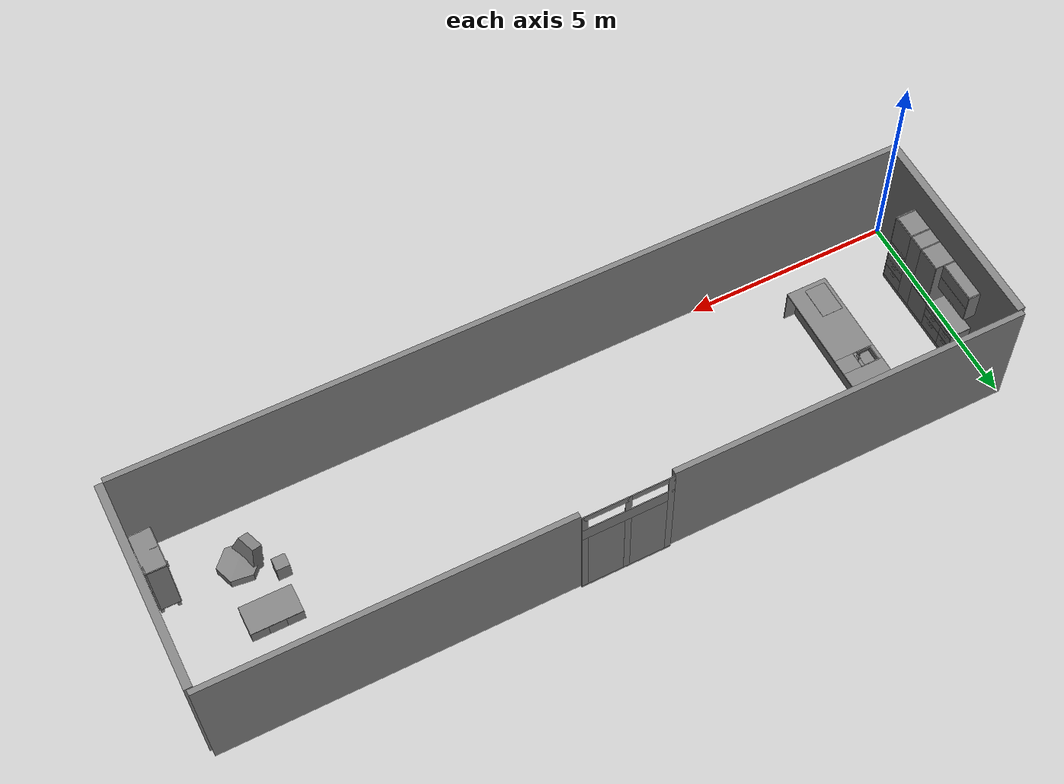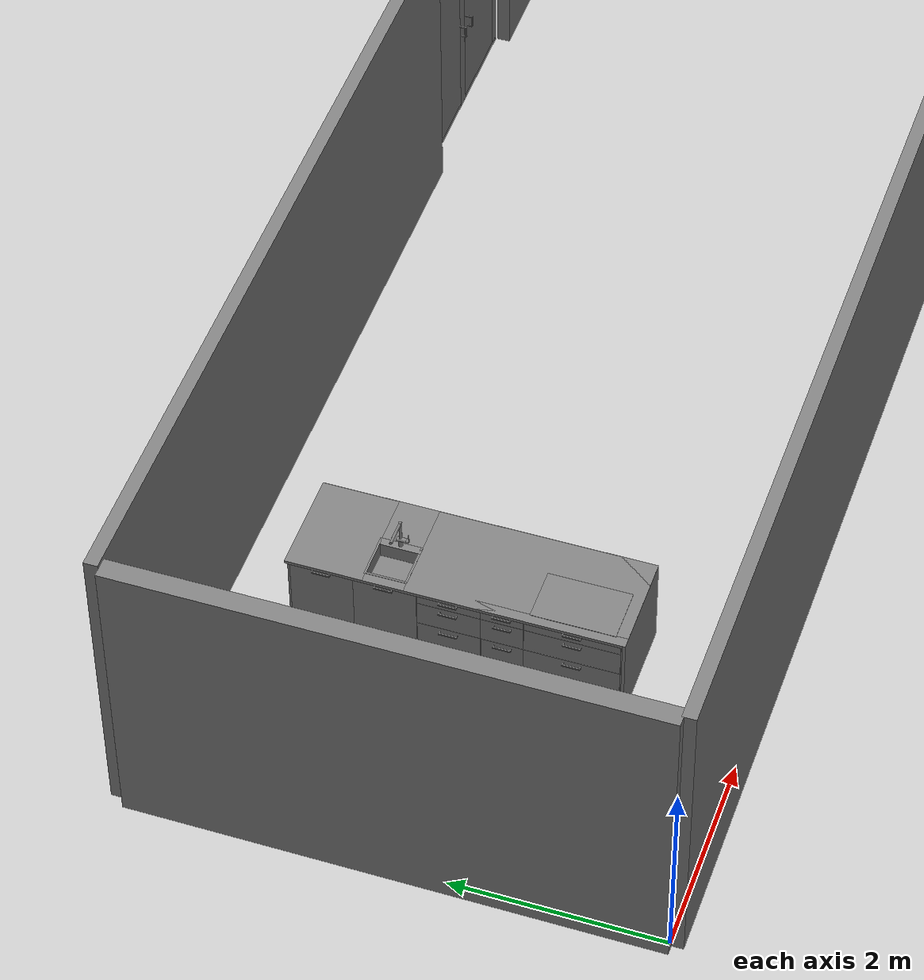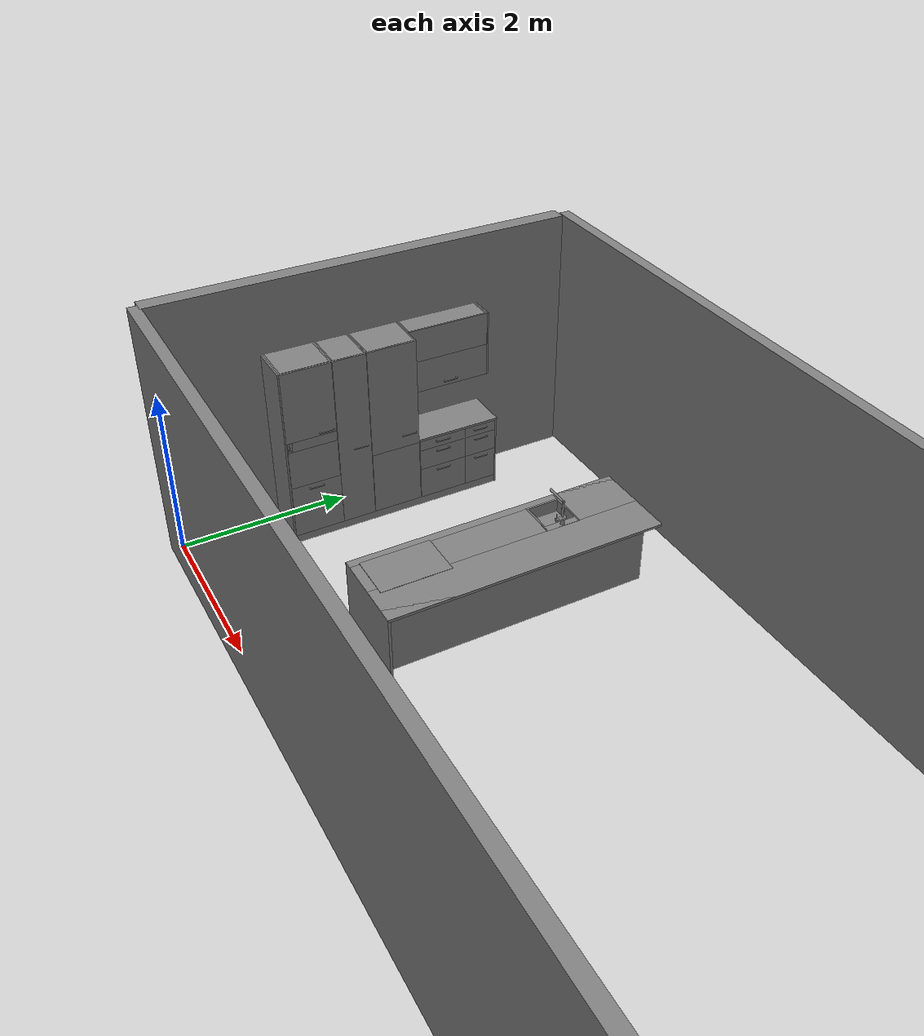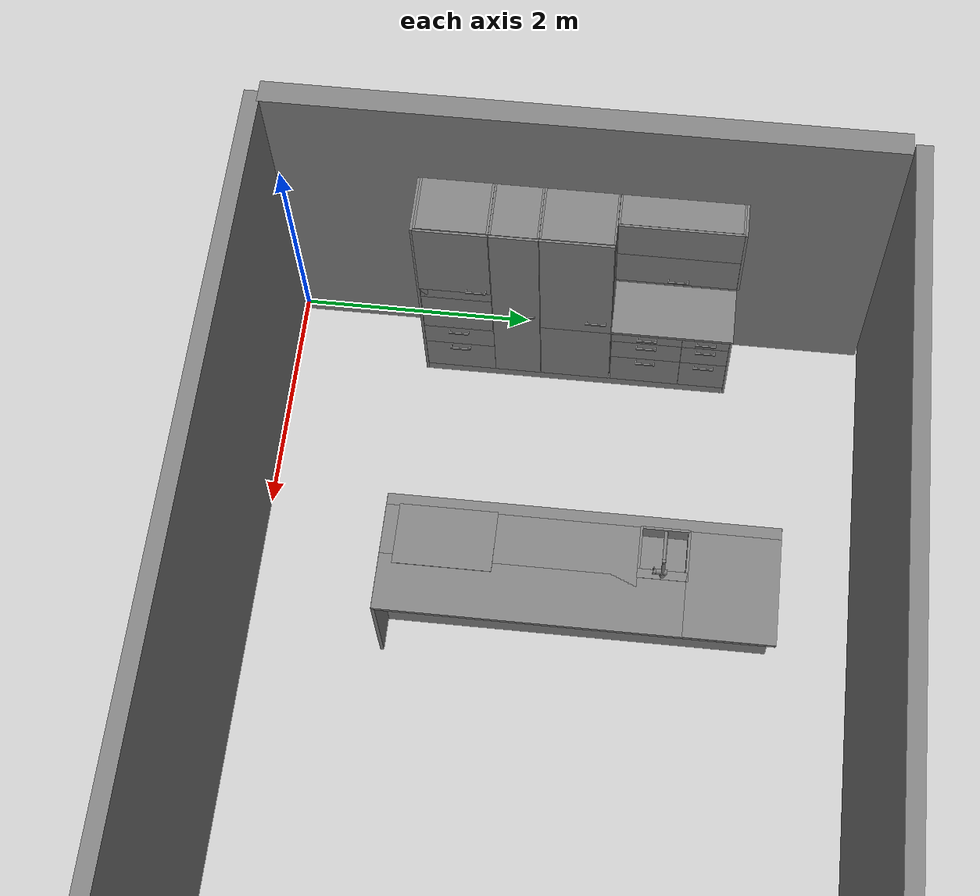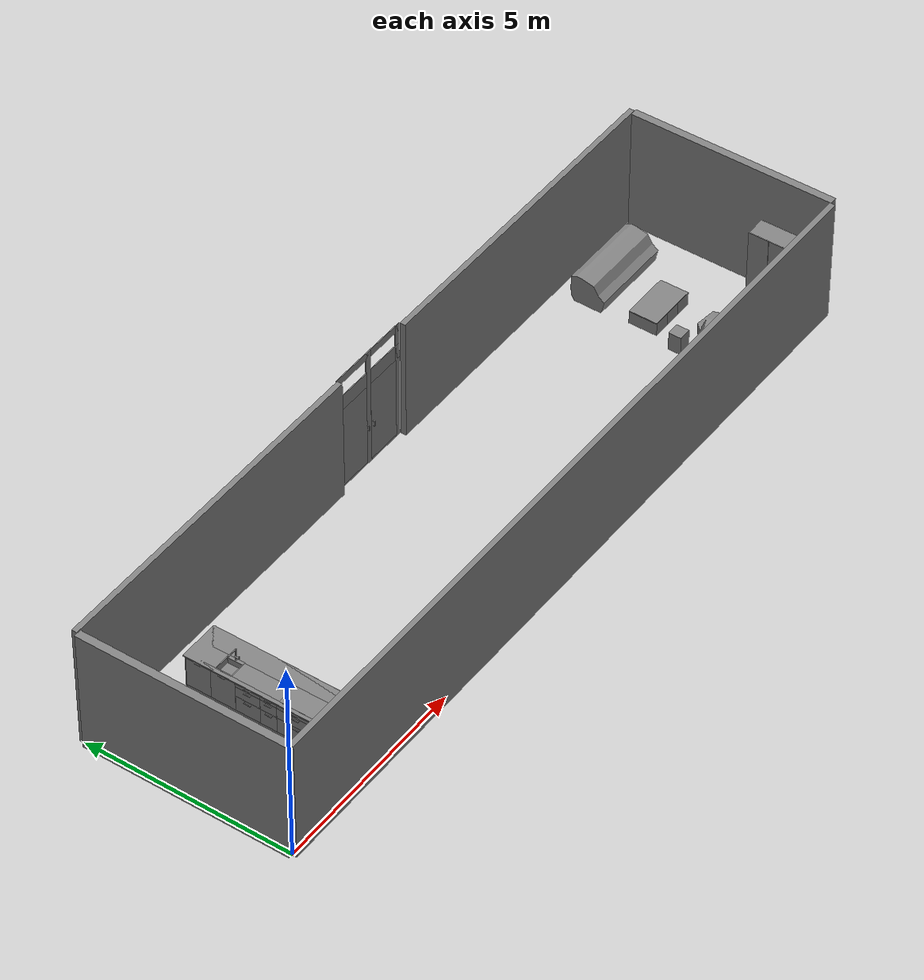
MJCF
<mujoco model="apartment">
    <compiler angle="radian" meshdir="apartment/stl/" autolimits="true" fusestatic="false" balanceinertia="true" discardvisual="true" boundmass="0.000001" boundinertia="0.000001"/>
    <statistic meansize="0.698866" extent="24.6878" center="9.40261 -0.0183012 1.53439"/>
    <asset>
        <mesh name="armchair" file="armchair.stl"/>
        <mesh name="sofa" file="sofa.stl"/>
    </asset>
    <worldbody>
        <body name="apartment">
            <body name="apartment_root">
                <body name="envelope_root" pos="8.85 1.75 0">
                    <body name="wall1" pos="0 0 -0.2">
                        <geom size="9.38022 0.06425 1.52585" pos="0.505224 -1.81425 1.73439" type="box"/>
                    </body>
                    <body name="wall2" pos="0 0 -0.2">
                        <geom size="0.094776 2.48345 1.52585" pos="-8.875 0.713447 1.73439" type="box"/>
                    </body>
                    <body name="wall3" pos="0 0 -0.2">
                        <geom size="4.23677 0.06425 1.52585" pos="-4.63823 3.27776 1.73439" type="box"/>
                        <geom size="4.1443 0.06425 1.52585" pos="5.87824 3.27776 1.73439" type="box"/>
                    </body>
                    <body name="wall4" pos="0 0 -0.2">
                        <geom size="0.094776 2.48345 1.52585" pos="9.98022 0.713447 1.73439" type="box"/>
                    </body>
                    <body name="windows" pos="0 0 -0.2"/>
                    <body name="window4_frame" pos="0.671098 3.37273 1.52145" quat="0.707107 0 0 -0.707107">
                        <geom size="0.01 1.0677 0.092776" pos="0 0 1.42883" type="box"/>
                        <geom size="0.01 1.0677 0.18914" pos="0 0 0.795222" type="box"/>
                        <geom size="0.01 1.0677 0.026796" pos="0 0 -1.49481" type="box"/>
                        <geom size="0.01 0.075574 1.52161" pos="0 0.992126 0" type="box"/>
                        <geom size="0.01 0.075574 1.52161" pos="0 -0.992126 0" type="box"/>
                        <geom size="0.01 0.073126 1.52161" type="box"/>
                        <body name="window4_right" pos="0 -0.916552 -0.425471">
                            <joint name="window4_right_joint" pos="0 0 0" axis="0 0 -1" range="0 1.5708"/>
                            <geom size="0.01 0.421713 1.03155" pos="0 0.421713 0" type="box"/>
                            <body name="window4_right_handle_rotation" pos="0.01 0.834107 0">
                                <joint name="window4_right_handle_rotation_joint" pos="0 0 0" axis="-1 0 0" range="0 1.5708"/>
                                <body name="window4_right_handle" pos="0.067235 0 -0.057755">
                                    <geom size="0.008 0.037618" pos="-0.029618 0 0.057814" quat="0.707107 0 0.707107 0" type="cylinder"/>
                                    <geom size="0.008 0.065813" type="cylinder"/>
                                    <geom size="0.008 0.026476" pos="-0.018476 0 -0.057813" quat="0.707107 0 0.707107 0" type="cylinder"/>
                                </body>
                            </body>
                        </body>
                        <body name="window4_left" pos="0.00162 0.929112 -0.425471">
                            <joint name="window4_left_joint" pos="0 0 0" axis="0 0 1" range="0 1.5708"/>
                            <geom size="0.01 0.43203 1.03155" pos="0 -0.43203 0" type="box"/>
                            <body name="window4_left_handle_rotation" pos="0.01 -0.834107 0">
                                <joint name="window4_left_handle_rotation_joint" pos="0 0 0" axis="1 0 0" range="0 1.5708"/>
                                <body name="window4_left_handle" pos="0.067235 0 -0.057755">
                                    <geom size="0.008 0.037618" pos="-0.029618 0 0.057814" quat="0.707107 0 0.707107 0" type="cylinder"/>
                                    <geom size="0.008 0.065813" type="cylinder"/>
                                    <geom size="0.008 0.026476" pos="-0.018476 0 -0.057813" quat="0.707107 0 0.707107 0" type="cylinder"/>
                                </body>
                            </body>
                        </body>
                    </body>
                </body>
                <body name="furnitures_root" pos="8.85 1.75 0">
                    <body name="wardrobe" pos="9.7082 -0.6331 0">
                        <geom size="0.04 0.04 0.075" pos="-0.2693 -0.4482 0.075" type="box"/>
                        <geom size="0.04 0.04 0.075" pos="0.10603 -0.4482 0.075" type="box"/>
                        <geom size="0.04 0.04 0.075" pos="-0.2693 0.4482 0.075" type="box"/>
                        <geom size="0.04 0.04 0.075" pos="0.10603 0.4482 0.075" type="box"/>
                        <geom size="0.2435 0.5 0.01345" pos="-0.0805 0 0.16345" type="box"/>
                        <geom size="0.2435 0.01035 0.825" pos="-0.0805 0.48965 0.975" type="box"/>
                        <geom size="0.2159 0.009284 0.825" pos="-0.0896 0 0.975" type="box"/>
                        <geom size="0.2435 0.01035 0.825" pos="-0.0805 -0.48965 0.975" type="box"/>
                        <geom size="0.01835 0.5 0.825" pos="0.14465 0 0.975" type="box"/>
                        <geom size="0.01835 0.5 0.825" pos="0.14465 0 0.975" type="box"/>
                        <geom size="0.2435 0.5 0.0135" pos="-0.0805 0 1.7865" type="box"/>
                        <geom size="0.21495 0.234979 0.0059" pos="-0.08861 -0.244343 0.5727" type="box"/>
                        <geom size="0.21495 0.234979 0.0059" pos="-0.08861 -0.244343 0.974836" type="box"/>
                        <geom size="0.21495 0.234979 0.0059" pos="-0.08861 -0.244343 1.37686" type="box"/>
                        <geom size="0.0075 0.234949" pos="-0.086923 0.244373 1.66898" quat="0.707105 0.707108 0 0" type="cylinder"/>
                        <body name="wardrobe_door_left" pos="-0.3246 0.5 0">
                            <joint name="wardrobe_door_left_joint" pos="0 0 0" axis="0 0 -1" range="0 1.5708"/>
                            <geom size="0.0064835 0.247719 0.82422" pos="-0.006435 -0.2485 0.975" type="box"/>
                            <body name="wardrobe_door_left_handle" pos="-0.032089 -0.460513 0.973703">
                                <geom size="0.016778 0.007541 0.0072935" pos="0.010421 0 0.059003" type="box"/>
                                <geom size="0.007243 0.007541 0.065" pos="-0.0136 0 0" type="box"/>
                                <geom size="0.016778 0.007541 0.0072935" pos="0.010421 0 -0.059003" type="box"/>
                            </body>
                        </body>
                        <body name="wardrobe_door_right" pos="-0.3246 -0.5 0">
                            <joint name="wardrobe_door_right_joint" pos="0 0 0" axis="0 0 1" range="0 1.5708"/>
                            <geom size="0.0064835 0.247719 0.82422" pos="-0.006435 0.2485 0.975" type="box"/>
                            <body name="wardrobe_door_right_handle" pos="-0.032089 0.460513 0.973703">
                                <geom size="0.016778 0.007541 0.0072935" pos="0.010421 0 0.059003" type="box"/>
                                <geom size="0.007243 0.007541 0.065" pos="-0.0136 0 0" type="box"/>
                                <geom size="0.016778 0.007541 0.0072935" pos="0.010421 0 -0.059003" type="box"/>
                            </body>
                        </body>
                    </body>
                    <body name="armchair" pos="7.9688 -0.3791 0.355943" quat="0.573561 0 0 0.819163">
                        <geom type="mesh" mesh="armchair"/>
                    </body>
                    <body name="sofa" pos="8.1986 2.4096 0.35733" quat="0.707107 0 0 0.707107">
                        <geom type="mesh" mesh="sofa"/>
                    </body>
                    <body name="coffee_table" pos="7.8034 1.02957 0" quat="0.707105 0 0 0.707108">
                        <geom size="0.29 0.54 0.02977" pos="0 0 0.02977" type="box"/>
                        <geom size="0.3053 0.2 0.00598" pos="-0.022101 0 0.06552" type="box"/>
                        <geom size="0.35 0.2 0.16" pos="0 0.39975 0.220625" type="box"/>
                        <geom size="0.35 0.2 0.16" pos="0 -0.39975 0.220625" type="box"/>
                        <geom size="0.03365 0.2 0.16" pos="0.316343 0 0.22" type="box"/>
                        <geom size="0.35 0.6 0.01" pos="0 0 0.39" type="box"/>
                        <body name="coffee_table_drawer">
                            <joint name="coffee_table_drawer_joint" pos="0 0 0" axis="-1 0 0" type="slide" range="0 0.5"/>
                            <geom size="0.0107 0.198 0.157845" pos="-0.338806 0 0.21892" type="box"/>
                            <geom size="0.27605 0.1727 0.01072" pos="-0.051066 0 0.107979" type="box"/>
                            <geom size="0.0107 0.1743 0.1199" pos="0.207974 0 0.238907" type="box"/>
                            <geom size="0.27605 0.0107 0.132125" pos="-0.051066 -0.186206 0.226597" type="box"/>
                            <geom size="0.27605 0.0107 0.132125" pos="-0.051066 0.186206 0.226597" type="box"/>
                        </body>
                    </body>
                    <body name="bedside_table" pos="7.211 0.1296 0.229905">
                        <geom size="0.156 0.156 0.23" type="box"/>
                    </body>
                </body>
                <body name="kitchen_root">
                    <body name="kitchen1_root">
                        <body name="cabinet1" pos="0.284632 1.46676 1.11441" quat="0 0 0 1">
                            <geom size="0.27747 0.0095 1.06389" pos="0.010499 -0.3 0.05" type="box"/>
                            <geom size="0.27747 0.0095 1.06389" pos="0.010499 0.280469 0.05" type="box"/>
                            <geom size="0.004 0.280969 1.05589" pos="0.271973 -0.009901 0.041995" type="box"/>
                            <geom size="0.287969 0.01046 1.11388" pos="0 0.299967 0" type="box"/>
                            <geom size="0.008 0.280969 0.032" pos="-0.254976 -0.009901 1.06578" type="box"/>
                            <geom size="0.270471 0.280969 0.008" pos="0.0055 -0.009901 1.10578" type="box"/>
                            <geom size="0.270471 0.280969 0.0075" pos="0.0005 -0.009901 0.249501" type="box"/>
                            <body name="cabinet1_shelf1" pos="0.009901 0.0005 0.56">
                                <geom size="0.280969 0.267471 0.0075" type="box" rgba="1 1 1 1"/>
                            </body>
                            <body name="cabinet1_shelf2" pos="0.009901 0.0005 0.249501">
                                <geom size="0.267471 0.280969 0.0075" type="box" rgba="1 1 1 1"/>
                            </body>
                            <body name="cabinet1_door" pos="-0.28 0.28 0.677">
                                <joint name="cabinet1_door_joint" pos="0 0 0" axis="0 0 -1" range="0 1.5708"/>
                                <geom size="0.0095 0.298468 0.433405" pos="0 -0.285091 0" type="box"/>
                                <body name="cabinet1_door_handle" pos="-0.0359888 -0.463156 -0.389834" quat="0.707107 0.707107 0 0">
                                    <geom size="0.01 0.0065 0.0065" pos="0.0164985 0 0.08" type="box"/>
                                    <geom size="0.01 0.0065 0.0065" pos="0.0164985 0 -0.08" type="box"/>
                                    <geom size="0.0065 0.0065 0.086516" type="box"/>
                                </body>
                            </body>
                            <body name="cabinet1_drawer1" pos="-0.0467902 -0.0112201 -0.486585">
                                <joint name="cabinet1_drawer1_joint" pos="0 0 0" axis="-1 0 0" type="slide" range="0 0.45"/>
                                <geom size="0.0095 0.298468 0.131486" pos="-0.233977 0 0" type="box"/>
                                <geom size="0.24585 0.0079221 0.0111962" pos="0.021336 -0.26865 0.0412455" type="box"/>
                                <geom size="0.24585 0.0079221 0.0111962" pos="0.021336 0.26865 0.0412455" type="box"/>
                                <geom size="0.24585 0.0079221 0.041748" pos="0.021336 -0.26865 -0.078968" type="box"/>
                                <geom size="0.24585 0.0079221 0.026549" pos="0.021336 0.26865 -0.0941" type="box"/>
                                <geom size="0.24578 0.26182 0.008" pos="0.021399 0 -0.114232" type="box"/>
                                <geom size="0.00932692 0.26182 0.084435" pos="0.26 0 -0.038" type="box"/>
                                <body name="cabinet1_drawer1_handle" pos="-0.268318 0.00091816 0.0840143" quat="0.707107 0.707107 0 0">
                                    <geom size="0.01 0.0065 0.0065" pos="0.0164985 0 0.08" type="box"/>
                                    <geom size="0.01 0.0065 0.0065" pos="0.0164985 0 -0.08" type="box"/>
                                    <geom size="0.0065 0.0065 0.086516" type="box"/>
                                </body>
                            </body>
                            <body name="cabinet1_drawer2" pos="-0.046 -0.011 -0.816">
                                <joint name="cabinet1_drawer2_joint" pos="0 0 0" axis="-1 0 0" type="slide" range="0 0.45"/>
                                <geom size="0.0095 0.298468 0.19714" pos="-0.233977 0 0" type="box"/>
                                <geom size="0.24585 0.0079221 0.0111962" pos="0.021336 -0.26865 -0.0084109" type="box"/>
                                <geom size="0.24585 0.0079221 0.0111962" pos="0.021336 0.26865 -0.0084109" type="box"/>
                                <geom size="0.24585 0.0079221 0.041751" pos="0.021336 -0.26865 -0.12854" type="box"/>
                                <geom size="0.24585 0.0079221 0.041751" pos="0.021336 0.26865 -0.12854" type="box"/>
                                <geom size="0.24578 0.26182 0.008" pos="0.021399 0 -0.16226" type="box"/>
                                <geom size="0.00932692 0.26182 0.0758612" pos="0.26 0 -0.0797358" type="box"/>
                                <body name="cabinet1_drawer2_handle" pos="-0.269483 -0.00145845 0.150606" quat="0.707107 0.707107 0 0">
                                    <geom size="0.01 0.0065 0.0065" pos="0.0164985 0 0.08" type="box"/>
                                    <geom size="0.01 0.0065 0.0065" pos="0.0164985 0 -0.08" type="box"/>
                                    <geom size="0.0065 0.0065 0.086516" type="box"/>
                                </body>
                            </body>
                            <body name="oven" pos="-0.273959 -0.0123597 -0.342672">
                                <geom size="0.272833 0.294945 0.075421" pos="0.264778 0.003055 0.50654" type="box"/>
                                <geom size="0.272833 0.294945 0.022799" pos="0.264778 0.003055 0.018039" type="box"/>
                                <geom size="0.272833 0.0295 0.293011" pos="0.264778 0.2675 0.288951" type="box"/>
                                <geom size="0.272833 0.027451 0.293011" pos="0.264778 0.264104 0.288951" type="box"/>
                                <geom size="0.037392 0.294945 0.293011" pos="0.5 -0.003055 0.288951" type="box"/>
                                <body name="oven_door" quat="0.5 0.5 0.5 -0.5">
                                    <joint name="oven_door_joint" pos="0 0 0" axis="0 0 1" range="0 1.5708"/>
                                    <geom size="0.235848 0.018499 0.295294" pos="-0.226757 0.005395 -0.002993" type="box"/>
                                </body>
                            </body>
                        </body>
                        <body name="cabinet2" pos="0.279909 1.97705 1.16239" quat="0 0 0 1">
                            <geom size="0.277359 0.008 1.06384" pos="0.005897 0.191979 0" type="box"/>
                            <geom size="0.277359 0.008 1.06384" pos="0.005897 -0.191979 0" type="box"/>
                            <geom size="0.277359 0.183882 0.008" pos="0.005897 0 1.05584" type="box"/>
                            <geom size="0.277359 0.183882 0.008" pos="0.005897 0 0.975845" type="box"/>
                            <geom size="0.277359 0.183882 0.008" pos="0.005897 0 -1.05594" type="box"/>
                            <geom size="0.007187 0.183882 0.031996" pos="-0.26039 0 1.01584" type="box"/>
                            <geom size="0.004 0.183882 1.04784" pos="0.267372 0 0" type="box"/>
                            <body name="cabinet2_door" pos="-0.284321 0.18657 0.00105865">
                                <joint name="cabinet2_door_joint" pos="0 0 0" axis="0 0 -1" range="0 1.5708"/>
                                <geom size="0.0095 0.198479 1.06138" pos="-0.000653 -0.185074 0" type="box"/>
                                <body name="cabinet2_door_handle" pos="-0.0218499 -0.25886 -0.105189" quat="0.707107 0.707107 0 0">
                                    <geom size="0.01 0.0065 0.0065" pos="0.0164985 0 0.08" type="box"/>
                                    <geom size="0.01 0.0065 0.0065" pos="0.0164985 0 -0.08" type="box"/>
                                    <geom size="0.0065 0.0065 0.086516" type="box"/>
                                </body>
                            </body>
                            <body name="cabinet2_shelf" pos="-0.00337784 0.00043732 0.790361">
                                <geom size="0.241474 0.183979 0.0075" pos="0 0 0.004951" type="box"/>
                            </body>
                            <body name="cabinet2_drawer1" pos="-0.00464775 0.00134538 0.580462">
                                <joint name="cabinet2_drawer1_joint" pos="0 0 0" axis="-1 0 0" type="slide" range="0 0.45"/>
                                <geom size="0.0085 0.180981 0.050495" pos="-0.242975 0 0" type="box"/>
                                <geom size="0.008064 0.180981 0.050495" pos="0.235441 0 0" type="box"/>
                                <geom size="0.247489 0.008 0.050495" pos="-0.003984 0.170578 0" type="box"/>
                                <geom size="0.247489 0.008 0.050495" pos="-0.003984 -0.170578 0" type="box"/>
                                <geom size="0.247489 0.180981 0.010749" pos="-0.003984 0 -0.039746" type="box"/>
                            </body>
                            <body name="cabinet2_drawer2" pos="-0.00464775 -0.00134538 0.422749">
                                <joint name="cabinet2_drawer2_joint" pos="0 0 0" axis="-1 0 0" type="slide" range="0 0.45"/>
                                <geom size="0.006898 0.180981 0.049" pos="-0.242374 0 -0.042" type="box"/>
                                <geom size="0.006898 0.180981 0.010149" pos="-0.242374 0 0.060843" type="box"/>
                                <geom size="0.008393 0.032441 0.09099" pos="-0.242869 0.148428 0" type="box"/>
                                <geom size="0.008393 0.032441 0.09099" pos="-0.242869 -0.148428 0" type="box"/>
                                <geom size="0.008064 0.180981 0.090879" pos="0.235441 0 0" type="box"/>
                                <geom size="0.247489 0.008 0.011649" pos="-0.003984 0.170578 0.075342" type="box"/>
                                <geom size="0.247489 0.008 0.011649" pos="-0.003984 -0.170578 0.075342" type="box"/>
                                <geom size="0.247489 0.008 0.043553" pos="-0.003984 0.170578 -0.043743" type="box"/>
                                <geom size="0.247489 0.008 0.043553" pos="-0.003984 -0.170578 -0.043743" type="box"/>
                                <geom size="0.247489 0.180981 0.010749" pos="-0.003984 0 -0.080242" type="box"/>
                            </body>
                            <body name="cabinet2_drawer3" pos="-0.00464775 -0.00134538 0.142897">
                                <joint name="cabinet2_drawer3_joint" pos="0 0 0" axis="-1 0 0" type="slide" range="0 0.45"/>
                                <geom size="0.006898 0.180981 0.049" pos="-0.242374 0 -0.042" type="box"/>
                                <geom size="0.006898 0.180981 0.010149" pos="-0.242374 0 0.060843" type="box"/>
                                <geom size="0.008393 0.032441 0.09099" pos="-0.242869 0.148428 0" type="box"/>
                                <geom size="0.008393 0.032441 0.09099" pos="-0.242869 -0.148428 0" type="box"/>
                                <geom size="0.008064 0.180981 0.090879" pos="0.235441 0 0" type="box"/>
                                <geom size="0.247489 0.008 0.011649" pos="-0.003984 0.170578 0.075342" type="box"/>
                                <geom size="0.247489 0.008 0.011649" pos="-0.003984 -0.170578 0.075342" type="box"/>
                                <geom size="0.247489 0.008 0.043553" pos="-0.003984 0.170578 -0.043743" type="box"/>
                                <geom size="0.247489 0.008 0.043553" pos="-0.003984 -0.170578 -0.043743" type="box"/>
                                <geom size="0.247489 0.180981 0.010749" pos="-0.003984 0 -0.080242" type="box"/>
                            </body>
                            <body name="cabinet2_drawer4" pos="-0.00464775 0.00134538 -0.242437">
                                <joint name="cabinet2_drawer4_joint" pos="0 0 0" axis="-1 0 0" type="slide" range="0 0.45"/>
                                <geom size="0.006898 0.180981 0.049" pos="-0.242374 0 -0.042" type="box"/>
                                <geom size="0.006898 0.180981 0.010149" pos="-0.242374 0 0.060843" type="box"/>
                                <geom size="0.008393 0.032441 0.09099" pos="-0.242869 0.148428 0" type="box"/>
                                <geom size="0.008393 0.032441 0.09099" pos="-0.242869 -0.148428 0" type="box"/>
                                <geom size="0.008064 0.180981 0.090879" pos="0.235441 0 0" type="box"/>
                                <geom size="0.247489 0.008 0.011649" pos="-0.003984 0.170578 0.075342" type="box"/>
                                <geom size="0.247489 0.008 0.011649" pos="-0.003984 -0.170578 0.075342" type="box"/>
                                <geom size="0.247489 0.008 0.043553" pos="-0.003984 0.170578 -0.043743" type="box"/>
                                <geom size="0.247489 0.008 0.043553" pos="-0.003984 -0.170578 -0.043743" type="box"/>
                                <geom size="0.247489 0.180981 0.010749" pos="-0.003984 0 -0.080242" type="box"/>
                            </body>
                            <body name="cabinet2_drawer5" pos="-0.00464775 0.00134538 -0.518096">
                                <joint name="cabinet2_drawer5_joint" pos="0 0 0" axis="-1 0 0" type="slide" range="0 0.45"/>
                                <geom size="0.006898 0.180981 0.049" pos="-0.242374 0 -0.042" type="box"/>
                                <geom size="0.006898 0.180981 0.010149" pos="-0.242374 0 0.060843" type="box"/>
                                <geom size="0.008393 0.032441 0.09099" pos="-0.242869 0.148428 0" type="box"/>
                                <geom size="0.008393 0.032441 0.09099" pos="-0.242869 -0.148428 0" type="box"/>
                                <geom size="0.008064 0.180981 0.090879" pos="0.235441 0 0" type="box"/>
                                <geom size="0.247489 0.008 0.011649" pos="-0.003984 0.170578 0.075342" type="box"/>
                                <geom size="0.247489 0.008 0.011649" pos="-0.003984 -0.170578 0.075342" type="box"/>
                                <geom size="0.247489 0.008 0.043553" pos="-0.003984 0.170578 -0.043743" type="box"/>
                                <geom size="0.247489 0.008 0.043553" pos="-0.003984 -0.170578 -0.043743" type="box"/>
                                <geom size="0.247489 0.180981 0.010749" pos="-0.003984 0 -0.080242" type="box"/>
                            </body>
                            <body name="cabinet2_drawer6" pos="-0.00464775 0.00134538 -0.955192">
                                <joint name="cabinet2_drawer6_joint" pos="0 0 0" axis="-1 0 0" type="slide" range="0 0.45"/>
                                <geom size="0.006898 0.180981 0.049" pos="-0.242374 0 -0.042" type="box"/>
                                <geom size="0.006898 0.180981 0.010149" pos="-0.242374 0 0.060843" type="box"/>
                                <geom size="0.008393 0.032441 0.09099" pos="-0.242869 0.148428 0" type="box"/>
                                <geom size="0.008393 0.032441 0.09099" pos="-0.242869 -0.148428 0" type="box"/>
                                <geom size="0.008064 0.180981 0.090879" pos="0.235441 0 0" type="box"/>
                                <geom size="0.247489 0.008 0.011649" pos="-0.003984 0.170578 0.075342" type="box"/>
                                <geom size="0.247489 0.008 0.011649" pos="-0.003984 -0.170578 0.075342" type="box"/>
                                <geom size="0.247489 0.008 0.043553" pos="-0.003984 0.170578 -0.043743" type="box"/>
                                <geom size="0.247489 0.008 0.043553" pos="-0.003984 -0.170578 -0.043743" type="box"/>
                                <geom size="0.247489 0.180981 0.010749" pos="-0.003984 0 -0.080242" type="box"/>
                            </body>
                        </body>
                        <body name="cabinet3" pos="0.274985 2.4799 1.16288" quat="0 0 0 1">
                            <geom size="0.277193 0.01 1.06382" pos="0.003155 -0.291968 0" type="box"/>
                            <geom size="0.277193 0.01 1.06382" pos="0.003155 0.291968 0" type="box"/>
                            <geom size="0.277193 0.286067 0.008" pos="0.003155 0 1.05584" type="box"/>
                            <geom size="0.277193 0.286067 0.008" pos="0.003155 0 0.895854" type="box"/>
                            <geom size="0.277193 0.286067 0.008" pos="0.003155 0 0.819863" type="box"/>
                            <geom size="0.277193 0.286067 0.008" pos="0.003155 0 -0.980943" type="box"/>
                            <geom size="0.277193 0.286067 0.008" pos="0.003155 0 -1.05594" type="box"/>
                            <geom size="0.0104594 0.286067 0.07201" pos="-0.262453 0 0.975825" type="box"/>
                            <geom size="0.0104594 0.286067 0.03" pos="-0.262453 0 0.857803" type="box"/>
                            <geom size="0.0104594 0.286067 0.03" pos="-0.262453 0 0.857803" type="box"/>
                            <geom size="0.008 0.073992 0.037346" pos="-0.264485 -0.20788 -1.02629" type="box"/>
                            <body name="fridge_door1" pos="-0.297259 0.299145 0.25674">
                                <joint name="fridge_door1_joint" pos="0 0 0" axis="0 0 -1" range="0 1.5708"/>
                                <geom size="0.009277 0.298246 0.668339" pos="0.006948 -0.297325 0.139709" type="box"/>
                                <geom size="0.0125 0.276867 0.494447" pos="0.03605 -0.295455 -0.001115" type="box"/>
                                <body name="fridge_door1_handle" pos="-0.027991 -0.465343 -0.3616" quat="0.707107 0.707107 0 0">
                                    <geom size="0.01 0.0065 0.0065" pos="0.0164985 0 0.08" type="box"/>
                                    <geom size="0.01 0.0065 0.0065" pos="0.0164985 0 -0.08" type="box"/>
                                    <geom size="0.0065 0.0065 0.086516" type="box"/>
                                </body>
                                <body name="fridge_door_tray1" pos="0.103791 -0.297261 -0.0156525">
                                    <geom size="0.001 0.210927 0.047787" pos="0.054273 0 0" type="box"/>
                                    <geom size="0.001 0.210927 0.047787" pos="-0.054273 0 0" type="box"/>
                                    <geom size="0.05471 0.001 0.047787" pos="0 0.209978 0" type="box"/>
                                    <geom size="0.05471 0.001 0.047787" pos="0 -0.209978 0" type="box"/>
                                    <geom size="0.05471 0.210927 0.001" pos="0 0 -0.047166" type="box"/>
                                </body>
                                <body name="fridge_door_tray2" pos="0.101769 -0.298471 0.223872">
                                    <geom size="0.001 0.210977 0.026901" pos="0.054019 0 0" type="box"/>
                                    <geom size="0.001 0.210977 0.026901" pos="-0.054019 0 0" type="box"/>
                                    <geom size="0.054994 0.001 0.026901" pos="0 0.209978 0" type="box"/>
                                    <geom size="0.054994 0.001 0.026901" pos="0 -0.209978 0" type="box"/>
                                    <geom size="0.054994 0.210977 0.001" pos="0 0 -0.025903" type="box"/>
                                    <body name="fridge_egg_tray" pos="-0.00226576 0.0853089 0.00069855"/>
                                </body>
                            </body>
                            <body name="fridge_door2" pos="-0.297259 0.29909 -0.638008">
                                <joint name="fridge_door2_joint" pos="0 0 0" axis="0 0 -1" range="0 1.5708"/>
                                <geom size="0.009277 0.298246 0.39297" pos="0.006948 -0.297325 -0.028308" type="box"/>
                                <geom size="0.0125 0.276867 0.311166" pos="0.03605 -0.295455 0.019366" type="box"/>
                                <body name="fridge_door2_handle" pos="0.0280466 -0.465383 0.317868" quat="0.707107 0.707107 0 0">
                                    <geom size="0.01 0.0065 0.0065" pos="0.0164985 0 0.08" type="box"/>
                                    <geom size="0.01 0.0065 0.0065" pos="0.0164985 0 -0.08" type="box"/>
                                    <geom size="0.0065 0.0065 0.086516" type="box"/>
                                </body>
                            </body>
                            <body name="fridge_base" pos="-0.0191809 -0.00292496 -0.0816938">
                                <geom size="0.241826 0.021622 0.879405" pos="0.016051 -0.257778 0" type="box"/>
                                <geom size="0.241826 0.021622 0.879405" pos="0.016051 0.257778 0" type="box"/>
                                <geom size="0.196424 0.012277 0.318196" pos="-0.029351 -0.223235 -0.561142" type="box"/>
                                <geom size="0.196424 0.012277 0.318196" pos="-0.029351 0.223235 -0.561142" type="box"/>
                                <geom size="0.246695 0.278217 0.023998" pos="0.011034 0 0.855407" type="box"/>
                                <geom size="0.196424 0.234783 0.03771" pos="-0.029351 0 0.839695" type="box"/>
                                <geom size="0.196424 0.234783 0.0125" pos="-0.029351 0 0.224975" type="box"/>
                                <geom size="0.196424 0.234783 0.058965" pos="-0.029351 0 -0.18398" type="box"/>
                                <geom size="0.196424 0.234783 0.036788" pos="-0.029351 0 -0.842617" type="box"/>
                                <geom size="0.00782 0.234783 0.464658" pos="0.159364 0 0.339754" type="box"/>
                                <geom size="0.058398 0.234783 0.281275" pos="0.199778 0 -0.524221" type="box"/>
                                <body name="fridge_shelf1" pos="-0.00102744 0.00204316 0.545451">
                                    <geom size="0.133991 0.234134 0.004544" type="box"/>
                                </body>
                                <body name="fridge_shelf2" pos="-0.00102744 0.00204316 0.411236">
                                    <geom size="0.133991 0.234134 0.004544" type="box"/>
                                </body>
                                <body name="fridge_drawer1" pos="-0.0120901 0.00223595 0.110257">
                                    <joint name="fridge_drawer1_joint" pos="0 0 0" axis="-1 0 0" type="slide" range="0 0.3"/>
                                    <geom size="0.0025 0.227117 0.011921" pos="-0.169309 0 0.070506" type="box"/>
                                    <geom size="0.001448 0.227117 0.047864" pos="-0.169309 0 -0.034598" type="box"/>
                                    <geom size="0.002123 0.227117 0.082076" pos="0.16468 0 0" type="box"/>
                                    <geom size="0.171761 0.00983 0.082076" pos="0 0.217307 0" type="box"/>
                                    <geom size="0.171761 0.00983 0.082076" pos="0 -0.217307 0" type="box"/>
                                    <geom size="0.171761 0.227117 0.001372" pos="0 0 -0.080999" type="box"/>
                                </body>
                                <body name="fridge_drawer2" pos="-0.0154834 -0.00198811 -0.0496125">
                                    <joint name="fridge_drawer2_joint" pos="0 0 0" axis="-1 0 0" type="slide" range="0 0.3"/>
                                    <geom size="0.0025 0.227117 0.011801" pos="-0.169309 0 0.057007" type="box"/>
                                    <geom size="0.001448 0.227117 0.032111" pos="-0.169309 0 -0.036775" type="box"/>
                                    <geom size="0.002123 0.227117 0.068941" pos="0.16468 0 0" type="box"/>
                                    <geom size="0.171761 0.00983 0.068941" pos="0 0.217307 0" type="box"/>
                                    <geom size="0.171761 0.00983 0.068941" pos="0 -0.217307 0" type="box"/>
                                    <geom size="0.171761 0.227117 0.001372" pos="0 0 -0.066161" type="box"/>
                                </body>
                                <body name="fridge_drawer3" pos="-0.032657 0.00251899 -0.356176">
                                    <joint name="fridge_drawer3_joint" pos="0 0 0" axis="-1 0 0" type="slide" range="0 0.3"/>
                                    <geom size="0.001 0.204478 0.012462" pos="-0.165482 0 0.083453" type="box"/>
                                    <geom size="0.001 0.204478 0.05887" pos="-0.165482 0 -0.037113" type="box"/>
                                    <geom size="0.001555 0.204478 0.095915" pos="0.154928 0 0" type="box"/>
                                    <geom size="0.161445 0.00732 0.095915" pos="-0.004962 0.197083 0" type="box"/>
                                    <geom size="0.161445 0.00732 0.095915" pos="-0.004962 -0.197083 0" type="box"/>
                                    <geom size="0.161445 0.204478 0.000911" pos="-0.004962 0 -0.095072" type="box"/>
                                </body>
                                <body name="fridge_drawer4" pos="-0.0288522 0.00508168 -0.532998">
                                    <joint name="fridge_drawer4_joint" pos="0 0 0" axis="-1 0 0" type="slide" range="0 0.3"/>
                                    <geom size="0.001 0.204478 0.012462" pos="-0.165482 0 0.063456" type="box"/>
                                    <geom size="0.001 0.204478 0.04" pos="-0.165482 0 -0.035978" type="box"/>
                                    <geom size="0.001 0.204478 0.075917" pos="0.155483 0 0" type="box"/>
                                    <geom size="0.166408 0.008 0.075917" pos="0 0.196311 0" type="box"/>
                                    <geom size="0.166408 0.008 0.075917" pos="0 -0.196311 0" type="box"/>
                                    <geom size="0.166408 0.204478 0.001" pos="0 0 -0.074992" type="box"/>
                                </body>
                                <body name="fridge_drawer5" pos="-0.0648077 0 -0.712787">
                                    <joint name="fridge_drawer5_joint" pos="0 0 0" axis="-1 0 0" type="slide" range="0 0.3"/>
                                    <geom size="0.001 0.204404 0.012499" pos="-0.120488 0 0.08099" type="box"/>
                                    <geom size="0.001 0.204404 0.055353" pos="-0.118669 0 -0.03813" type="box"/>
                                    <geom size="0.003217 0.204404 0.075917" pos="0.108269 0 0" type="box"/>
                                    <geom size="0.120421 0.007461 0.075917" pos="0 0.196942 0" type="box"/>
                                    <geom size="0.120421 0.007461 0.075917" pos="0 -0.196942 0" type="box"/>
                                    <geom size="0.120421 0.204404 0.001" pos="0 0 -0.09249" type="box"/>
                                </body>
                            </body>
                        </body>
                        <body name="cabinet4" pos="0.182244 3.29388 1.82711" quat="0 0 0 1">
                            <geom size="0.005 0.483948 0.38291" pos="0.168984 0.010048 0" type="box"/>
                            <geom size="0.174981 0.008 0.398908" pos="0.01 0.501898 0" type="box"/>
                            <geom size="0.174981 0.008 0.398908" pos="0.01 -0.481997 0" type="box"/>
                            <geom size="0.184869 0.01 0.398908" pos="0 -0.5 0" type="box"/>
                            <geom size="0.168981 0.483948 0.008" pos="0.004 0.010048 0.390908" type="box"/>
                            <geom size="0.168981 0.483948 0.008" pos="0.004 0.010048 -0.391007" type="box"/>
                            <body name="cabinet4_door1" pos="-0.172261 0.00837158 0.199167">
                                <geom size="0.0095 0.497446 0.197868" pos="-0.002895 0 0" type="box"/>
                            </body>
                            <body name="cabinet4_door2" pos="-0.150429 0.0093109 -0.199949">
                                <geom size="0.0095 0.497446 0.197868" pos="-0.025359 0 0" type="box"/>
                                <body name="cabinet4_door2_handle" pos="-0.0610386 -0.0141519 -0.133571" quat="0.707107 0.707107 0 0">
                                    <geom size="0.01 0.0065 0.0065" pos="0.0164985 0 0.08" type="box"/>
                                    <geom size="0.01 0.0065 0.0065" pos="0.0164985 0 -0.08" type="box"/>
                                    <geom size="0.0065 0.0065 0.086516" type="box"/>
                                </body>
                            </body>
                            <body name="cabinet4_shelf1" pos="0.00833792 -0.0101648 0.125006">
                                <geom size="0.153539 0.483948 0.004042" type="box"/>
                            </body>
                            <body name="cabinet4_shelf2" pos="0.00833792 -0.0101648 -0.0984018">
                                <geom size="0.153539 0.483948 0.004042" type="box"/>
                            </body>
                        </body>
                        <body name="counter_wall" pos="0.281428 3.29494 0.908921" quat="0 0 0 1">
                            <geom size="0.2995 0.515532 0.013389" type="box"/>
                        </body>
                        <body name="cabinet5" pos="0.274766 3.08412 0.494207" quat="0 0 0 1">
                            <geom size="0.27726 0.008 0.399006" pos="0 0.291968 0" type="box"/>
                            <geom size="0.27726 0.008 0.399006" pos="0 -0.291968 0" type="box"/>
                            <geom size="0.27726 0.284067 0.008" pos="0 0 -0.391006" type="box"/>
                            <geom size="0.04 0.284067 0.008" pos="0.217476 0 0.390909" type="box"/>
                            <geom size="0.004 0.284067 0.38291" pos="0.261473 0 0" type="box"/>
                            <body name="cabinet5_drawer1" pos="-0.052627 -0.00100026 0.331778">
                                <joint name="cabinet5_drawer1_joint" pos="0 0 0" axis="-1 0 0" type="slide" range="0 0.45"/>
                                <geom size="0.245507 0.008 0.042633" pos="0.021031 0.270267 -0.01336" type="box"/>
                                <geom size="0.245507 0.008 0.042633" pos="0.021031 -0.270267 -0.01336" type="box"/>
                                <geom size="0.0095 0.298468 0.064993" pos="-0.233977 0 0" type="box"/>
                                <geom size="0.008 0.269804 0.042633" pos="0.260372 0 -0.01336" type="box"/>
                                <geom size="0.245507 0.269804 0.0075" pos="0.021031 0 -0.047595" type="box"/>
                                <body name="cabinet5_drawer1_handle" pos="-0.269809 0.00142363 0.0167695" quat="0.707107 0.707107 0 0">
                                    <geom size="0.01 0.0065 0.0065" pos="0.0164985 0 0.08" type="box"/>
                                    <geom size="0.01 0.0065 0.0065" pos="0.0164985 0 -0.08" type="box"/>
                                    <geom size="0.0065 0.0065 0.086516" type="box"/>
                                </body>
                            </body>
                            <body name="cabinet5_drawer2" pos="-0.0530376 -0.00079152 0.133725">
                                <joint name="cabinet5_drawer2_joint" pos="0 0 0" axis="-1 0 0" type="slide" range="0 0.45"/>
                                <geom size="0.245507 0.008 0.011649" pos="0.021031 0.270267 0.041246" type="box"/>
                                <geom size="0.245507 0.008 0.011649" pos="0.021031 -0.270267 0.041246" type="box"/>
                                <geom size="0.245507 0.008 0.041748" pos="0.021031 0.270267 -0.078968" type="box"/>
                                <geom size="0.245507 0.008 0.041748" pos="0.021031 -0.270267 -0.078968" type="box"/>
                                <geom size="0.0095 0.298468 0.131375" pos="-0.233977 0 0" type="box"/>
                                <geom size="0.008 0.269804 0.084491" pos="0.260372 0 -0.037996" type="box"/>
                                <geom size="0.245507 0.269804 0.008" pos="0.021031 0 -0.113735" type="box"/>
                                <body name="cabinet5_drawer2_handle" pos="-0.270711 0.00106413 0.0850084" quat="0.707107 0.707107 0 0">
                                    <geom size="0.01 0.0065 0.0065" pos="0.0164985 0 0.08" type="box"/>
                                    <geom size="0.01 0.0065 0.0065" pos="0.0164985 0 -0.08" type="box"/>
                                    <geom size="0.0065 0.0065 0.086516" type="box"/>
                                </body>
                            </body>
                            <body name="cabinet5_drawer3" pos="-0.0534509 -0.00075551 -0.195667">
                                <joint name="cabinet5_drawer3_joint" pos="0 0 0" axis="-1 0 0" type="slide" range="0 0.45"/>
                                <geom size="0.245507 0.008 0.011638" pos="0.021031 0.270267 -0.00926" type="box"/>
                                <geom size="0.245507 0.008 0.011638" pos="0.021031 -0.270267 -0.00926" type="box"/>
                                <geom size="0.245507 0.008 0.041711" pos="0.021031 0.270267 -0.129424" type="box"/>
                                <geom size="0.245507 0.008 0.041711" pos="0.021031 -0.270267 -0.129424" type="box"/>
                                <geom size="0.0095 0.298468 0.197867" pos="-0.233977 0 0" type="box"/>
                                <geom size="0.008 0.269804 0.084105" pos="0.260372 0 -0.088821" type="box"/>
                                <geom size="0.245507 0.269804 0.008" pos="0.021031 0 -0.164582" type="box"/>
                                <body name="cabinet5_drawer3_handle" pos="-0.268882 0.00102875 0.15027" quat="0.707107 0.707107 0 0">
                                    <geom size="0.01 0.0065 0.0065" pos="0.0164985 0 0.08" type="box"/>
                                    <geom size="0.01 0.0065 0.0065" pos="0.0164985 0 -0.08" type="box"/>
                                    <geom size="0.0065 0.0065 0.086516" type="box"/>
                                </body>
                            </body>
                        </body>
                        <body name="cabinet6" pos="0.274766 3.58384 0.494207" quat="0 0 0 1">
                            <geom size="0.27726 0.008 0.399006" pos="0 0.191779 0" type="box"/>
                            <geom size="0.27726 0.008 0.399006" pos="0 -0.191779 0" type="box"/>
                            <geom size="0.27726 0.184833 0.008" pos="0 0 -0.391006" type="box"/>
                            <geom size="0.04 0.184833 0.008" pos="0.217476 0 0.390909" type="box"/>
                            <geom size="0.004 0.184833 0.38291" pos="0.261473 0 0" type="box"/>
                            <body name="cabinet6_drawer1" pos="-0.053296 -0.00032649 0.331778">
                                <joint name="cabinet6_drawer1_joint" pos="0 0 0" axis="-1 0 0" type="slide" range="0 0.45"/>
                                <geom size="0.245507 0.008 0.042633" pos="0.021031 0.170562 -0.01336" type="box"/>
                                <geom size="0.245507 0.008 0.042633" pos="0.021031 -0.170562 -0.01336" type="box"/>
                                <geom size="0.0095 0.198867 0.064993" pos="-0.233977 0 0" type="box"/>
                                <geom size="0.008 0.178822 0.042633" pos="0.260372 0 -0.01336" type="box"/>
                                <geom size="0.245507 0.178822 0.0075" pos="0.021031 0 -0.047595" type="box"/>
                                <body name="cabinet6_drawer1_handle" pos="-0.266623 -0.00124599 0.0172039" quat="0.707107 0.707107 0 0">
                                    <geom size="0.01 0.0065 0.0065" pos="0.0164985 0 0.08" type="box"/>
                                    <geom size="0.01 0.0065 0.0065" pos="0.0164985 0 -0.08" type="box"/>
                                    <geom size="0.0065 0.0065 0.086516" type="box"/>
                                </body>
                            </body>
                            <body name="cabinet6_drawer2" pos="-0.0530569 -0.00074397 0.132969">
                                <joint name="cabinet6_drawer2_joint" pos="0 0 0" axis="-1 0 0" type="slide" range="0 0.45"/>
                                <geom size="0.245507 0.008 0.011649" pos="0.021031 0.170562 0.041246" type="box"/>
                                <geom size="0.245507 0.008 0.011649" pos="0.021031 -0.170562 0.041246" type="box"/>
                                <geom size="0.245507 0.008 0.041748" pos="0.021031 0.170562 -0.078968" type="box"/>
                                <geom size="0.245507 0.008 0.041748" pos="0.021031 -0.170562 -0.078968" type="box"/>
                                <geom size="0.0095 0.198867 0.131375" pos="-0.233977 0 0" type="box"/>
                                <geom size="0.008 0.178822 0.084491" pos="0.260372 0 -0.037996" type="box"/>
                                <geom size="0.245507 0.178822 0.008" pos="0.021031 0 -0.113735" type="box"/>
                                <body name="cabinet6_drawer2_handle" pos="-0.266862 -0.00397854 0.0854179" quat="0.707107 0.707107 0 0">
                                    <geom size="0.01 0.0065 0.0065" pos="0.0164985 0 0.08" type="box"/>
                                    <geom size="0.01 0.0065 0.0065" pos="0.0164985 0 -0.08" type="box"/>
                                    <geom size="0.0065 0.0065 0.086516" type="box"/>
                                </body>
                            </body>
                            <body name="cabinet6_drawer3" pos="-0.0527976 -0.00069453 -0.196909">
                                <joint name="cabinet6_drawer3_joint" pos="0 0 0" axis="-1 0 0" type="slide" range="0 0.45"/>
                                <geom size="0.245507 0.008 0.011638" pos="0.021031 0.170562 -0.00926" type="box"/>
                                <geom size="0.245507 0.008 0.011638" pos="0.021031 -0.170562 -0.00926" type="box"/>
                                <geom size="0.245507 0.008 0.041711" pos="0.021031 0.170562 -0.129424" type="box"/>
                                <geom size="0.245507 0.008 0.041711" pos="0.021031 -0.170562 -0.129424" type="box"/>
                                <geom size="0.0095 0.198867 0.197867" pos="-0.233977 0 0" type="box"/>
                                <geom size="0.008 0.178822 0.084105" pos="0.260372 0 -0.088821" type="box"/>
                                <geom size="0.245507 0.178822 0.008" pos="0.021031 0 -0.164582" type="box"/>
                                <body name="cabinet6_drawer3_handle" pos="-0.267122 -0.00402777 0.151166" quat="0.707107 0.707107 0 0">
                                    <geom size="0.01 0.0065 0.0065" pos="0.0164985 0 0.08" type="box"/>
                                    <geom size="0.01 0.0065 0.0065" pos="0.0164985 0 -0.08" type="box"/>
                                    <geom size="0.0065 0.0065 0.086516" type="box"/>
                                </body>
                            </body>
                        </body>
                        <body name="island_cover4" pos="0.272592 3.79516 0.446017" quat="0 0 0 1">
                            <geom size="0.296074 0.009554 0.448506" type="box"/>
                        </body>
                        <body name="kitchen1_base_board" pos="0.55976 2.47826 0.0516843" quat="0 0 0 1">
                            <geom size="0.009889 1.30158 0.05" type="box"/>
                        </body>
                    </body>
                    <body name="kitchen2_root" pos="0.1 0 0">
                        <body name="counter_sink_stove" pos="2.65274 2.70904 0.465629">
                            <geom size="0.5 0.0145 0.467231" pos="0 -1.5755 0" type="box"/>
                            <geom size="0.237531 1.58852 0.015" pos="0.262968 0 0.453637" type="box"/>
                            <geom size="0.048817 1.58852 0.015" pos="-0.451058 0 0.453637" type="box"/>
                            <geom size="0.498 0.367711 0.015" pos="0 1.22213 0.453637" type="box"/>
                            <geom size="0.498 1.02804 0.015" pos="0 -0.560551 0.453637" type="box"/>
                            <body name="stove" pos="-0.156557 -1.08145 0.471606">
                                <geom size="0.258 0.3975 0.002401" type="box"/>
                            </body>
                            <body name="counter_sink" pos="-0.188876 0.665534 0.382404">
                                <geom size="0.038996 0.202106 0.088694" pos="0.18348 0 0" type="box"/>
                                <geom size="0.01 0.202106 0.088694" pos="-0.212477 0 0" type="box"/>
                                <geom size="0.222309 0.01 0.088694" pos="0 -0.192479 0" type="box"/>
                                <geom size="0.222309 0.01 0.088694" pos="0 0.192479 0" type="box"/>
                                <geom size="0.222309 0.202106 0.013701" pos="0 0 -0.074992" type="box"/>
                                <body name="counter_watertab" pos="0.0767719 -0.0196184 0.238987">
                                    <geom size="0.022435 0.038739" pos="0.113704 0.0195 -0.11162" type="cylinder"/>
                                    <geom size="0.014 0.10908" pos="0.113704 0.0195 0.041404" type="cylinder"/>
                                    <geom size="0.010966 0.003818" pos="-0.116237 0.0195 0.121328" type="cylinder"/>
                                    <geom size="0.022466 0.044495" pos="0.113731 0.009 -0.073523" quat="0.5 -0.5 0.5 0.5" type="cylinder"/>
                                    <geom size="0.018" pos="0.113738 -0.035496 -0.073492"/>
                                    <geom size="0.014 0.131986" pos="-0.00425 0.019498 0.136485" quat="0.5 0.5 0.5 0.5" type="cylinder"/>
                                    <body name="counter_sink_tap_switch" pos="0.113711 -0.0405528 -0.0737045" quat="0 0 0 1">
                                        <joint name="counter_sink_tap_temperature_joint" pos="0 0 0" axis="0 -1 0" range="-1.5708 1.5708"/>
                                        <geom size="0.0005 0.0005 0.0005" type="box"/>
                                        <body name="counter_sink_tap">
                                            <joint name="counter_sink_switch_joint" pos="0 0 0" axis="-1 0 0" range="0 0.392699"/>
                                            <geom size="0.022432 0.012197" pos="0 0.007501 0" quat="0.5 -0.5 0.5 0.5" type="cylinder"/>
                                            <geom size="0.005 0.027997" pos="0 0.012886 0.048989" type="cylinder"/>
                                        </body>
                                    </body>
                                </body>
                            </body>
                        </body>
                        <body name="dishwasher" pos="2.32419 3.96355 0.162264">
                            <geom size="0.197879 0.007724 0.420898" pos="0.244142 0.291193 0.25785" type="box"/>
                            <geom size="0.197879 0.007724 0.420898" pos="0.244142 -0.291193 0.25785" type="box"/>
                            <geom size="0.064761 0.007724 0.351941" pos="-0.018498 0.291193 0.328806" type="box"/>
                            <geom size="0.064761 0.007724 0.351941" pos="-0.018498 -0.291193 0.328806" type="box"/>
                            <geom size="0.002413 0.298917 0.420898" pos="0.439555 0 0.25785" type="box"/>
                            <geom size="0.258487 0.298917 0.006749" pos="0.183466 0 0.671998" type="box"/>
                            <geom size="0.258487 0.298917 0.083552" pos="0.183466 0 -0.079608" type="box"/>
                            <body name="dishwasher_front" pos="-0.0761212 0.00031149 0.00728645" quat="0.707107 -0.707107 0 0">
                                <joint name="dishwasher_front_joint" pos="0 0 0" axis="0 0 -1" range="0 1.5708"/>
                                <geom size="0.009444 0.397179 0.304987" pos="-0.04 -0.329015 0" type="box"/>
                                <geom size="0.015 0.339603 0.287469" pos="-0.01 -0.334215 -0.015728" type="box"/>
                                <body name="dishwasher_front_handle" pos="-0.0749352 -0.678848 0">
                                    <geom size="0.01 0.0065 0.0065" pos="0.0164985 0 0.08" type="box"/>
                                    <geom size="0.01 0.0065 0.0065" pos="0.0164985 0 -0.08" type="box"/>
                                    <geom size="0.0065 0.0065 0.086516" type="box"/>
                                </body>
                            </body>
                            <body name="dishwasher_tray1" pos="0.224014 0.00735926 0.227136">
                                <joint name="dishwasher_tray1_joint" pos="0 0 0" axis="-1 0 0" type="slide" range="0 0.5"/>
                                <geom size="0.242135 0.269203 0.007112" pos="-0.03859 0 -0.144673" type="box"/>
                                <geom size="0.242135 0.005448 0.116486" pos="-0.03859 0.255159 -0.035299" type="box"/>
                                <geom size="0.242135 0.005448 0.116486" pos="-0.03859 -0.255159 -0.035299" type="box"/>
                                <geom size="0.004289 0.269203 0.116486" pos="0.193489 0 -0.035299" type="box"/>
                                <geom size="0.004289 0.269203 0.116486" pos="-0.280937 0 -0.035299" type="box"/>
                            </body>
                            <body name="dishwasher_tray2" pos="0.20742 0.00735798 0.402328">
                                <joint name="dishwasher_tray2_joint" pos="0 0 0" axis="-1 0 0" type="slide" range="0 0.3"/>
                                <geom size="0.231314 0.23732 0.013794" pos="0 0 -0.051928" type="box"/>
                                <geom size="0.231314 0.008574 0.087812" pos="0 -0.243352 0.023995" type="box"/>
                                <geom size="0.231314 0.008574 0.087812" pos="0 0.243352 0.023995" type="box"/>
                                <geom size="0.004182 0.23732 0.087812" pos="-0.225859 0 0.023995" type="box"/>
                                <geom size="0.004182 0.23732 0.087812" pos="0.225859 0 0.023995" type="box"/>
                            </body>
                            <body name="dishwasher_tray3" pos="0.227872 0.0131252 0.611314">
                                <joint name="dishwasher_tray3_joint" pos="0 0 0" axis="-1 0 0" type="slide" range="0 0.3"/>
                                <geom size="0.22 0.27 0.036" type="box"/>
                            </body>
                        </body>
                        <body name="cabinet8" pos="2.49268 3.37232 0.494481">
                            <geom size="0.277025 0.007942 0.398895" pos="0 0.291912 0" type="box"/>
                            <geom size="0.277025 0.007942 0.398895" pos="0 -0.291912 0" type="box"/>
                            <geom size="0.003944 0.284067 0.382909" pos="0.26153 0 0" type="box"/>
                            <geom size="0.04 0.284067 0.008" pos="0.217476 0 0.39091" type="box"/>
                            <geom size="0.277025 0.284067 0.008" pos="0 0 -0.391005" type="box"/>
                            <body name="sink_drawer1" pos="-0.0508662 0.00013535 0.0032">
                                <joint name="sink_drawer1_joint" pos="0 0 0" axis="-1 0 0" type="slide" range="0 0.45"/>
                                <geom size="0.009388 0.298258 0.397013" pos="-0.233976 0 0" type="box"/>
                                <geom size="0.009017 0.269754 0.084742" pos="0.259483 0 -0.288887" type="box"/>
                                <geom size="0.249028 0.0075 0.042" pos="0.025012 -0.268047 -0.08949" type="box"/>
                                <geom size="0.249028 0.0075 0.042" pos="0.025012 0.268047 -0.08949" type="box"/>
                                <geom size="0.249028 0.0075 0.011648" pos="0.025012 -0.268047 -0.208727" type="box"/>
                                <geom size="0.249028 0.0075 0.011648" pos="0.025012 0.268047 -0.208727" type="box"/>
                                <geom size="0.249028 0.0075 0.043609" pos="0.025012 -0.268047 -0.33085" type="box"/>
                                <geom size="0.249028 0.0075 0.043609" pos="0.025012 0.268047 -0.33085" type="box"/>
                                <geom size="0.249028 0.031012 0.008" pos="0.025012 -0.246033 -0.04" type="box"/>
                                <geom size="0.249028 0.031012 0.008" pos="0.025012 0.246033 -0.04" type="box"/>
                                <geom size="0.010504 0.277046 0.008" pos="-0.213959 0 -0.04" type="box"/>
                                <geom size="0.058653 0.277046 0.008" pos="0.21583 0 -0.04" type="box"/>
                                <geom size="0.074789 0.008426 0.173305" pos="0.086505 0.00535 -0.198155" type="box"/>
                                <geom size="0.074789 0.008426 0.173305" pos="0.086505 0.211412 -0.198155" type="box"/>
                                <geom size="0.008356 0.109826 0.173305" pos="0.152938 0.109826 -0.198155" type="box"/>
                                <geom size="0.008356 0.109826 0.173305" pos="0.02 0.109826 -0.198155" type="box"/>
                                <geom size="0.074789 0.109826 0.00085" pos="0.086505 0.109826 -0.372315" type="box"/>
                                <geom size="0.074789 0.008426 0.173305" pos="0.086505 -0.00535 -0.198155" type="box"/>
                                <geom size="0.074789 0.008426 0.173305" pos="0.086505 -0.211412 -0.198155" type="box"/>
                                <geom size="0.008426 0.109826 0.173305" pos="0.152938 -0.109826 -0.198155" type="box"/>
                                <geom size="0.008426 0.109826 0.173305" pos="0.02 -0.109826 -0.198155" type="box"/>
                                <geom size="0.074789 0.109826 0.00085" pos="0.086505 -0.109826 -0.372315" type="box"/>
                                <geom size="0.109729 0.008426 0.173305" pos="-0.098209 0.221355 -0.198155" type="box"/>
                                <geom size="0.109729 0.008426 0.173305" pos="-0.098209 0.088435 -0.198155" type="box"/>
                                <geom size="0.008426 0.074691 0.173305" pos="0.003041 0.155 -0.198155" type="box"/>
                                <geom size="0.008426 0.074691 0.173305" pos="-0.199821 0.155 -0.198155" type="box"/>
                                <geom size="0.109729 0.074691 0.00085" pos="-0.098209 0.155 -0.372315" type="box"/>
                                <geom size="0.109729 0.008426 0.173305" pos="-0.098209 -0.221355 -0.198155" type="box"/>
                                <geom size="0.109729 0.008426 0.173305" pos="-0.098209 0.071323 -0.198155" type="box"/>
                                <geom size="0.008426 0.154749 0.173305" pos="0.003041 -0.075302 -0.198155" type="box"/>
                                <geom size="0.008426 0.154749 0.173305" pos="-0.199821 -0.075302 -0.198155" type="box"/>
                                <geom size="0.109729 0.154749 0.00085" pos="-0.098209 -0.075302 -0.372315" type="box"/>
                                <body name="sink_drawer1_handle" pos="-0.269002 0.00331339 0.350717" quat="0.707107 0.707107 0 0">
                                    <geom size="0.01 0.0065 0.0065" pos="0.0164985 0 0.08" type="box"/>
                                    <geom size="0.01 0.0065 0.0065" pos="0.0164985 0 -0.08" type="box"/>
                                    <geom size="0.0065 0.0065 0.086516" type="box"/>
                                </body>
                            </body>
                            <body name="sink_drawer2" pos="-0.0729948 0.00142344 0.164377">
                                <joint name="sink_drawer2_joint" pos="0 0 0" axis="-1 0 0" type="slide" range="0 0.3"/>
                                <geom size="0.188013 0.008 0.041105" pos="0.002535 0.270604 -0.000733" type="box"/>
                                <geom size="0.188013 0.008 0.041105" pos="0.002535 -0.270604 -0.000733" type="box"/>
                                <geom size="0.0085 0.032497 0.049661" pos="-0.191981 0.248473 0.000834" type="box"/>
                                <geom size="0.0085 0.032497 0.049661" pos="-0.191981 -0.248473 0.000834" type="box"/>
                                <geom size="0.0085 0.216977 0.049" pos="-0.191981 0 -0.0015" type="box"/>
                                <geom size="0.008 0.278678 0.0415" pos="0.184382 0 -0.0024" type="box"/>
                                <geom size="0.188013 0.278678 0.008" pos="0.002535 0 -0.036496" type="box"/>
                            </body>
                        </body>
                        <body name="cabinet9" pos="2.49288 2.77269 0.494068">
                            <geom size="0.277025 0.007942 0.398895" pos="0 0.291912 0" type="box"/>
                            <geom size="0.277025 0.007942 0.398895" pos="0 -0.291912 0" type="box"/>
                            <geom size="0.003944 0.284067 0.382909" pos="0.26153 0 0" type="box"/>
                            <geom size="0.04 0.284067 0.008" pos="0.217476 0 0.39091" type="box"/>
                            <geom size="0.277025 0.284067 0.008" pos="0 0 -0.391005" type="box"/>
                            <body name="cabinet9_drawer1" pos="-0.0507959 -0.00175364 0.332084">
                                <joint name="cabinet9_drawer1_joint" pos="0 0 0" axis="-1 0 0" type="slide" range="0 0.45"/>
                                <geom size="0.245507 0.008 0.042633" pos="0.021031 0.270267 -0.01336" type="box"/>
                                <geom size="0.245507 0.008 0.042633" pos="0.021031 -0.270267 -0.01336" type="box"/>
                                <geom size="0.0095 0.298468 0.064993" pos="-0.233977 0 0" type="box"/>
                                <geom size="0.008 0.269804 0.042633" pos="0.260372 0 -0.01336" type="box"/>
                                <geom size="0.245507 0.269804 0.0075" pos="0.021031 0 -0.047595" type="box"/>
                                <body name="cabinet9_drawer1_handle" pos="-0.269809 0.00142363 0.0167695" quat="0.707107 0.707107 0 0">
                                    <geom size="0.01 0.0065 0.0065" pos="0.0164985 0 0.08" type="box"/>
                                    <geom size="0.01 0.0065 0.0065" pos="0.0164985 0 -0.08" type="box"/>
                                    <geom size="0.0065 0.0065 0.086516" type="box"/>
                                </body>
                            </body>
                            <body name="cabinet9_drawer2" pos="-0.050753 -0.00065196 0.134945">
                                <joint name="cabinet9_drawer2_joint" pos="0 0 0" axis="-1 0 0" type="slide" range="0 0.45"/>
                                <geom size="0.245507 0.008 0.011649" pos="0.021031 0.270267 0.041246" type="box"/>
                                <geom size="0.245507 0.008 0.011649" pos="0.021031 -0.270267 0.041246" type="box"/>
                                <geom size="0.245507 0.008 0.041748" pos="0.021031 0.270267 -0.078968" type="box"/>
                                <geom size="0.245507 0.008 0.041748" pos="0.021031 -0.270267 -0.078968" type="box"/>
                                <geom size="0.0095 0.298468 0.131375" pos="-0.233977 0 0" type="box"/>
                                <geom size="0.008 0.269804 0.084491" pos="0.260372 0 -0.037996" type="box"/>
                                <geom size="0.245507 0.269804 0.008" pos="0.021031 0 -0.113735" type="box"/>
                                <body name="cabinet9_drawer2_handle" pos="-0.270711 0.00106413 0.0850084" quat="0.707107 0.707107 0 0">
                                    <geom size="0.01 0.0065 0.0065" pos="0.0164985 0 0.08" type="box"/>
                                    <geom size="0.01 0.0065 0.0065" pos="0.0164985 0 -0.08" type="box"/>
                                    <geom size="0.0065 0.0065 0.086516" type="box"/>
                                </body>
                            </body>
                            <body name="cabinet9_drawer3" pos="-0.0504523 -0.00167063 -0.196113">
                                <joint name="cabinet9_drawer3_joint" pos="0 0 0" axis="-1 0 0" type="slide" range="0 0.45"/>
                                <geom size="0.245507 0.008 0.011638" pos="0.021031 0.270267 -0.00926" type="box"/>
                                <geom size="0.245507 0.008 0.011638" pos="0.021031 -0.270267 -0.00926" type="box"/>
                                <geom size="0.245507 0.008 0.041711" pos="0.021031 0.270267 -0.129424" type="box"/>
                                <geom size="0.245507 0.008 0.041711" pos="0.021031 -0.270267 -0.129424" type="box"/>
                                <geom size="0.0095 0.298468 0.197867" pos="-0.233977 0 0" type="box"/>
                                <geom size="0.008 0.269804 0.084105" pos="0.260372 0 -0.088821" type="box"/>
                                <geom size="0.245507 0.269804 0.008" pos="0.021031 0 -0.164582" type="box"/>
                                <body name="cabinet9_drawer3_handle" pos="-0.268882 0.00102875 0.15027" quat="0.707107 0.707107 0 0">
                                    <geom size="0.01 0.0065 0.0065" pos="0.0164985 0 0.08" type="box"/>
                                    <geom size="0.01 0.0065 0.0065" pos="0.0164985 0 -0.08" type="box"/>
                                    <geom size="0.0065 0.0065 0.086516" type="box"/>
                                </body>
                            </body>
                        </body>
                        <body name="cabinet10" pos="2.49299 2.27192 0.50112">
                            <geom size="0.27726 0.008 0.399006" pos="0 0.191779 0" type="box"/>
                            <geom size="0.27726 0.008 0.399006" pos="0 -0.191779 0" type="box"/>
                            <geom size="0.27726 0.184833 0.008" pos="0 0 -0.391006" type="box"/>
                            <geom size="0.04 0.184833 0.008" pos="0.217476 0 0.390909" type="box"/>
                            <geom size="0.004 0.184833 0.38291" pos="0.261473 0 0" type="box"/>
                            <body name="cabinet10_drawer1" pos="-0.0509572 0.00062459 0.325652">
                                <joint name="cabinet10_drawer1_joint" pos="0 0 0" axis="-1 0 0" type="slide" range="0 0.45"/>
                                <geom size="0.245507 0.008 0.042633" pos="0.021031 0.170562 -0.01336" type="box"/>
                                <geom size="0.245507 0.008 0.042633" pos="0.021031 -0.170562 -0.01336" type="box"/>
                                <geom size="0.0095 0.198867 0.064993" pos="-0.233977 0 0" type="box"/>
                                <geom size="0.008 0.178822 0.042633" pos="0.260372 0 -0.01336" type="box"/>
                                <geom size="0.245507 0.178822 0.0075" pos="0.021031 0 -0.047595" type="box"/>
                                <body name="cabinet10_drawer1_handle" pos="-0.266623 -0.00124599 0.0172039" quat="0.707107 0.707107 0 0">
                                    <geom size="0.01 0.0065 0.0065" pos="0.0164985 0 0.08" type="box"/>
                                    <geom size="0.01 0.0065 0.0065" pos="0.0164985 0 -0.08" type="box"/>
                                    <geom size="0.0065 0.0065 0.086516" type="box"/>
                                </body>
                            </body>
                            <body name="cabinet10_drawer2" pos="-0.0507138 -6.861e-05 0.128052">
                                <joint name="cabinet10_drawer2_joint" pos="0 0 0" axis="-1 0 0" type="slide" range="0 0.45"/>
                                <geom size="0.245507 0.008 0.011649" pos="0.021031 0.170562 0.041246" type="box"/>
                                <geom size="0.245507 0.008 0.011649" pos="0.021031 -0.170562 0.041246" type="box"/>
                                <geom size="0.245507 0.008 0.041748" pos="0.021031 0.170562 -0.078968" type="box"/>
                                <geom size="0.245507 0.008 0.041748" pos="0.021031 -0.170562 -0.078968" type="box"/>
                                <geom size="0.0095 0.198867 0.131375" pos="-0.233977 0 0" type="box"/>
                                <geom size="0.008 0.178822 0.084491" pos="0.260372 0 -0.037996" type="box"/>
                                <geom size="0.245507 0.178822 0.008" pos="0.021031 0 -0.113735" type="box"/>
                                <body name="cabinet10_drawer2_handle" pos="-0.266862 -0.00397854 0.0854179" quat="0.707107 0.707107 0 0">
                                    <geom size="0.01 0.0065 0.0065" pos="0.0164985 0 0.08" type="box"/>
                                    <geom size="0.01 0.0065 0.0065" pos="0.0164985 0 -0.08" type="box"/>
                                    <geom size="0.0065 0.0065 0.086516" type="box"/>
                                </body>
                            </body>
                            <body name="cabinet10_drawer3" pos="-0.0504031 -0.00036921 -0.203967">
                                <joint name="cabinet10_drawer3_joint" pos="0 0 0" axis="-1 0 0" type="slide" range="0 0.45"/>
                                <geom size="0.245507 0.008 0.011638" pos="0.021031 0.170562 -0.00926" type="box"/>
                                <geom size="0.245507 0.008 0.011638" pos="0.021031 -0.170562 -0.00926" type="box"/>
                                <geom size="0.245507 0.008 0.041711" pos="0.021031 0.170562 -0.129424" type="box"/>
                                <geom size="0.245507 0.008 0.041711" pos="0.021031 -0.170562 -0.129424" type="box"/>
                                <geom size="0.0095 0.198867 0.197867" pos="-0.233977 0 0" type="box"/>
                                <geom size="0.008 0.178822 0.084105" pos="0.260372 0 -0.088821" type="box"/>
                                <geom size="0.245507 0.178822 0.008" pos="0.021031 0 -0.164582" type="box"/>
                                <body name="cabinet10_drawer3_handle" pos="-0.267122 -0.00402777 0.151166" quat="0.707107 0.707107 0 0">
                                    <geom size="0.01 0.0065 0.0065" pos="0.0164985 0 0.08" type="box"/>
                                    <geom size="0.01 0.0065 0.0065" pos="0.0164985 0 -0.08" type="box"/>
                                    <geom size="0.0065 0.0065 0.086516" type="box"/>
                                </body>
                            </body>
                        </body>
                        <body name="cabinet11" pos="2.49294 1.62156 0.509844">
                            <geom size="0.27726 0.008 0.399006" pos="0 -0.441952 0" type="box"/>
                            <geom size="0.27726 0.008 0.399006" pos="0 -0.441952 0" type="box"/>
                            <geom size="0.27726 0.43394 0.008" pos="0 0 -0.391006" type="box"/>
                            <geom size="0.04 0.43394 0.008" pos="0.217476 0 0.390909" type="box"/>
                            <geom size="0.004 0.43394 0.38291" pos="0.261473 0 0" type="box"/>
                            <body name="cabinet11_drawer1" pos="-0.0508224 0.00063939 0.318169">
                                <joint name="cabinet11_drawer1_joint" pos="0 0 0" axis="-1 0 0" type="slide" range="0 0.45"/>
                                <geom size="0.245507 0.008 0.042633" pos="0.021031 0.418233 -0.01336" type="box"/>
                                <geom size="0.245507 0.008 0.042633" pos="0.021031 -0.418233 -0.01336" type="box"/>
                                <geom size="0.0095 0.448341 0.064993" pos="-0.233977 0 0" type="box"/>
                                <geom size="0.008 0.419788 0.042633" pos="0.260372 0 -0.01336" type="box"/>
                                <geom size="0.245507 0.419788 0.0075" pos="0.021031 0 -0.047595" type="box"/>
                                <body name="cabinet11_drawer1_handle" pos="-0.266623 -0.00124599 0.0172039" quat="0.707107 0.707107 0 0">
                                    <geom size="0.01 0.0065 0.0065" pos="0.0164985 0 0.08" type="box"/>
                                    <geom size="0.01 0.0065 0.0065" pos="0.0164985 0 -0.08" type="box"/>
                                    <geom size="0.0065 0.0065 0.086516" type="box"/>
                                </body>
                            </body>
                            <body name="cabinet11_drawer2" pos="-0.0503088 0.0004598 0.119178">
                                <joint name="cabinet11_drawer2_joint" pos="0 0 0" axis="-1 0 0" type="slide" range="0 0.45"/>
                                <geom size="0.245507 0.008 0.011649" pos="0.021031 0.418233 0.041246" type="box"/>
                                <geom size="0.245507 0.008 0.011649" pos="0.021031 -0.418233 0.041246" type="box"/>
                                <geom size="0.245507 0.008 0.041748" pos="0.021031 0.418233 -0.078968" type="box"/>
                                <geom size="0.245507 0.008 0.041748" pos="0.021031 -0.418233 -0.078968" type="box"/>
                                <geom size="0.0095 0.448341 0.131375" pos="-0.233977 0 0" type="box"/>
                                <geom size="0.008 0.419788 0.084491" pos="0.260372 0 -0.037996" type="box"/>
                                <geom size="0.245507 0.419788 0.008" pos="0.021031 0 -0.113735" type="box"/>
                                <body name="cabinet11_drawer2_handle" pos="-0.266862 -0.00397854 0.0854179" quat="0.707107 0.707107 0 0">
                                    <geom size="0.01 0.0065 0.0065" pos="0.0164985 0 0.08" type="box"/>
                                    <geom size="0.01 0.0065 0.0065" pos="0.0164985 0 -0.08" type="box"/>
                                    <geom size="0.0065 0.0065 0.086516" type="box"/>
                                </body>
                            </body>
                            <body name="cabinet11_drawer3" pos="-0.0507751 0.00146352 -0.213308">
                                <joint name="cabinet11_drawer3_joint" pos="0 0 0" axis="-1 0 0" type="slide" range="0 0.45"/>
                                <geom size="0.245507 0.008 0.011638" pos="0.021031 0.418233 -0.00926" type="box"/>
                                <geom size="0.245507 0.008 0.011638" pos="0.021031 -0.418233 -0.00926" type="box"/>
                                <geom size="0.245507 0.008 0.041711" pos="0.021031 0.418233 -0.129424" type="box"/>
                                <geom size="0.245507 0.008 0.041711" pos="0.021031 -0.418233 -0.129424" type="box"/>
                                <geom size="0.0095 0.448341 0.197867" pos="-0.233977 0 0" type="box"/>
                                <geom size="0.008 0.419788 0.084105" pos="0.260372 0 -0.088821" type="box"/>
                                <geom size="0.245507 0.419788 0.008" pos="0.021031 0 -0.164582" type="box"/>
                                <body name="cabinet11_drawer3_handle" pos="-0.267122 -0.00402777 0.151166" quat="0.707107 0.707107 0 0">
                                    <geom size="0.01 0.0065 0.0065" pos="0.0164985 0 0.08" type="box"/>
                                    <geom size="0.01 0.0065 0.0065" pos="0.0164985 0 -0.08" type="box"/>
                                    <geom size="0.0065 0.0065 0.086516" type="box"/>
                                </body>
                            </body>
                        </body>
                        <body name="kitchen2_base_board" pos="2.21094 2.40968 0.0496364">
                            <geom size="0.01 1.55624 0.05" pos="0 0.3023 0" type="box"/>
                        </body>
                        <body name="island_cover1" pos="2.86825 2.7196 0.450317">
                            <geom size="0.009625 1.56783 0.451805" type="box"/>
                        </body>
                        <body name="island_cover3" pos="2.53831 4.2773 0.45176">
                            <geom size="0.339444 0.01 0.451805" type="box"/>
                        </body>
                        <body name="island_cover5" pos="2.5375 1.16089 0.446014">
                            <geom size="0.339444 0.01 0.451805" type="box"/>
                        </body>
                    </body>
                </body>
            </body>
        </body>
    </worldbody>
    <equality/>
    <contact>
        <exclude body1="window4_right" body2="window4_frame"/>
        <exclude body1="window4_right_handle_rotation" body2="window4_right"/>
        <exclude body1="window4_left" body2="window4_frame"/>
        <exclude body1="window4_left_handle_rotation" body2="window4_left"/>
        <exclude body1="wardrobe_door_left" body2="wardrobe"/>
        <exclude body1="wardrobe_door_right" body2="wardrobe"/>
        <exclude body1="coffee_table_drawer" body2="coffee_table"/>
        <exclude body1="cabinet1_door" body2="cabinet1"/>
        <exclude body1="cabinet1_drawer1" body2="cabinet1"/>
        <exclude body1="cabinet1_drawer2" body2="cabinet1"/>
        <exclude body1="oven_door" body2="oven"/>
        <exclude body1="cabinet2_door" body2="cabinet2"/>
        <exclude body1="cabinet2_drawer1" body2="cabinet2"/>
        <exclude body1="cabinet2_drawer2" body2="cabinet2"/>
        <exclude body1="cabinet2_drawer3" body2="cabinet2"/>
        <exclude body1="cabinet2_drawer4" body2="cabinet2"/>
        <exclude body1="cabinet2_drawer5" body2="cabinet2"/>
        <exclude body1="cabinet2_drawer6" body2="cabinet2"/>
        <exclude body1="fridge_door1" body2="cabinet3"/>
        <exclude body1="fridge_door2" body2="cabinet3"/>
        <exclude body1="fridge_drawer1" body2="fridge_base"/>
        <exclude body1="fridge_drawer2" body2="fridge_base"/>
        <exclude body1="fridge_drawer3" body2="fridge_base"/>
        <exclude body1="fridge_drawer4" body2="fridge_base"/>
        <exclude body1="fridge_drawer5" body2="fridge_base"/>
        <exclude body1="cabinet5_drawer1" body2="cabinet5"/>
        <exclude body1="cabinet5_drawer2" body2="cabinet5"/>
        <exclude body1="cabinet5_drawer3" body2="cabinet5"/>
        <exclude body1="cabinet6_drawer1" body2="cabinet6"/>
        <exclude body1="cabinet6_drawer2" body2="cabinet6"/>
        <exclude body1="cabinet6_drawer3" body2="cabinet6"/>
        <exclude body1="counter_sink_tap_switch" body2="counter_watertab"/>
        <exclude body1="counter_sink_tap" body2="counter_sink_tap_switch"/>
        <exclude body1="dishwasher_front" body2="dishwasher"/>
        <exclude body1="dishwasher_tray1" body2="dishwasher"/>
        <exclude body1="dishwasher_tray2" body2="dishwasher"/>
        <exclude body1="dishwasher_tray3" body2="dishwasher"/>
        <exclude body1="sink_drawer1" body2="cabinet8"/>
        <exclude body1="sink_drawer2" body2="cabinet8"/>
        <exclude body1="cabinet9_drawer1" body2="cabinet9"/>
        <exclude body1="cabinet9_drawer2" body2="cabinet9"/>
        <exclude body1="cabinet9_drawer3" body2="cabinet9"/>
        <exclude body1="cabinet10_drawer1" body2="cabinet10"/>
        <exclude body1="cabinet10_drawer2" body2="cabinet10"/>
        <exclude body1="cabinet10_drawer3" body2="cabinet10"/>
        <exclude body1="cabinet11_drawer1" body2="cabinet11"/>
        <exclude body1="cabinet11_drawer2" body2="cabinet11"/>
        <exclude body1="cabinet11_drawer3" body2="cabinet11"/>
        <exclude body1="cabinet1" body2="cabinet1_door_handle"/>
        <exclude body1="cabinet1" body2="cabinet1_drawer1_handle"/>
        <exclude body1="cabinet1" body2="cabinet1_drawer2_handle"/>
        <exclude body1="cabinet10" body2="cabinet10_drawer1_handle"/>
        <exclude body1="cabinet10" body2="cabinet10_drawer2_handle"/>
        <exclude body1="cabinet10" body2="cabinet10_drawer3_handle"/>
        <exclude body1="cabinet10_drawer1" body2="cabinet10_drawer1_handle"/>
        <exclude body1="cabinet10_drawer1" body2="cabinet10_drawer2_handle"/>
        <exclude body1="cabinet10_drawer1" body2="cabinet10_drawer3_handle"/>
        <exclude body1="cabinet10_drawer1_handle" body2="cabinet10_drawer2_handle"/>
        <exclude body1="cabinet10_drawer1_handle" body2="cabinet10_drawer3_handle"/>
        <exclude body1="cabinet10_drawer2" body2="cabinet10_drawer1_handle"/>
        <exclude body1="cabinet10_drawer2" body2="cabinet10_drawer2_handle"/>
        <exclude body1="cabinet10_drawer2" body2="cabinet10_drawer3_handle"/>
        <exclude body1="cabinet10_drawer2_handle" body2="cabinet10_drawer3_handle"/>
        <exclude body1="cabinet10_drawer3" body2="cabinet10_drawer1_handle"/>
        <exclude body1="cabinet10_drawer3" body2="cabinet10_drawer2_handle"/>
        <exclude body1="cabinet10_drawer3" body2="cabinet10_drawer3_handle"/>
        <exclude body1="cabinet11" body2="cabinet11_drawer1_handle"/>
        <exclude body1="cabinet11" body2="cabinet11_drawer2_handle"/>
        <exclude body1="cabinet11" body2="cabinet11_drawer3_handle"/>
        <exclude body1="cabinet11_drawer1" body2="cabinet11_drawer1_handle"/>
        <exclude body1="cabinet11_drawer1" body2="cabinet11_drawer2_handle"/>
        <exclude body1="cabinet11_drawer1" body2="cabinet11_drawer3_handle"/>
        <exclude body1="cabinet11_drawer1_handle" body2="cabinet11_drawer2_handle"/>
        <exclude body1="cabinet11_drawer1_handle" body2="cabinet11_drawer3_handle"/>
        <exclude body1="cabinet11_drawer2" body2="cabinet11_drawer1_handle"/>
        <exclude body1="cabinet11_drawer2" body2="cabinet11_drawer2_handle"/>
        <exclude body1="cabinet11_drawer2" body2="cabinet11_drawer3_handle"/>
        <exclude body1="cabinet11_drawer2_handle" body2="cabinet11_drawer3_handle"/>
        <exclude body1="cabinet11_drawer3" body2="cabinet11_drawer1_handle"/>
        <exclude body1="cabinet11_drawer3" body2="cabinet11_drawer2_handle"/>
        <exclude body1="cabinet11_drawer3" body2="cabinet11_drawer3_handle"/>
        <exclude body1="cabinet1_door" body2="cabinet1_shelf1"/>
        <exclude body1="cabinet1_door" body2="cabinet1_shelf2"/>
        <exclude body1="cabinet1_door" body2="cabinet1_door_handle"/>
        <exclude body1="cabinet1_door" body2="cabinet1_drawer1_handle"/>
        <exclude body1="cabinet1_door" body2="cabinet1_drawer2_handle"/>
        <exclude body1="cabinet1_door" body2="oven"/>
        <exclude body1="cabinet1_door_handle" body2="cabinet1_shelf1"/>
        <exclude body1="cabinet1_door_handle" body2="cabinet1_shelf2"/>
        <exclude body1="cabinet1_door_handle" body2="cabinet1_drawer1_handle"/>
        <exclude body1="cabinet1_door_handle" body2="cabinet1_drawer2_handle"/>
        <exclude body1="cabinet1_door_handle" body2="oven"/>
        <exclude body1="cabinet1_drawer1" body2="cabinet1_shelf1"/>
        <exclude body1="cabinet1_drawer1" body2="cabinet1_shelf2"/>
        <exclude body1="cabinet1_drawer1" body2="cabinet1_door_handle"/>
        <exclude body1="cabinet1_drawer1" body2="cabinet1_drawer1_handle"/>
        <exclude body1="cabinet1_drawer1" body2="cabinet1_drawer2_handle"/>
        <exclude body1="cabinet1_drawer1" body2="oven"/>
        <exclude body1="cabinet1_drawer1_handle" body2="cabinet1_shelf1"/>
        <exclude body1="cabinet1_drawer1_handle" body2="cabinet1_shelf2"/>
        <exclude body1="cabinet1_drawer1_handle" body2="cabinet1_drawer2_handle"/>
        <exclude body1="cabinet1_drawer1_handle" body2="oven"/>
        <exclude body1="cabinet1_drawer2" body2="cabinet1_shelf1"/>
        <exclude body1="cabinet1_drawer2" body2="cabinet1_shelf2"/>
        <exclude body1="cabinet1_drawer2" body2="cabinet1_door_handle"/>
        <exclude body1="cabinet1_drawer2" body2="cabinet1_drawer1_handle"/>
        <exclude body1="cabinet1_drawer2" body2="cabinet1_drawer2_handle"/>
        <exclude body1="cabinet1_drawer2" body2="oven"/>
        <exclude body1="cabinet1_drawer2_handle" body2="cabinet1_shelf1"/>
        <exclude body1="cabinet1_drawer2_handle" body2="cabinet1_shelf2"/>
        <exclude body1="cabinet1_drawer2_handle" body2="oven"/>
        <exclude body1="cabinet2" body2="cabinet2_door_handle"/>
        <exclude body1="cabinet2_door" body2="cabinet2_door_handle"/>
        <exclude body1="cabinet2_door" body2="cabinet2_shelf"/>
        <exclude body1="cabinet2_door_handle" body2="cabinet2_shelf"/>
        <exclude body1="cabinet2_drawer1" body2="cabinet2_door_handle"/>
        <exclude body1="cabinet2_drawer1" body2="cabinet2_shelf"/>
        <exclude body1="cabinet2_drawer2" body2="cabinet2_door_handle"/>
        <exclude body1="cabinet2_drawer2" body2="cabinet2_shelf"/>
        <exclude body1="cabinet2_drawer3" body2="cabinet2_door_handle"/>
        <exclude body1="cabinet2_drawer3" body2="cabinet2_shelf"/>
        <exclude body1="cabinet2_drawer4" body2="cabinet2_door_handle"/>
        <exclude body1="cabinet2_drawer4" body2="cabinet2_shelf"/>
        <exclude body1="cabinet2_drawer5" body2="cabinet2_door_handle"/>
        <exclude body1="cabinet2_drawer5" body2="cabinet2_shelf"/>
        <exclude body1="cabinet2_drawer6" body2="cabinet2_door_handle"/>
        <exclude body1="cabinet2_drawer6" body2="cabinet2_shelf"/>
        <exclude body1="cabinet3" body2="fridge_door1_handle"/>
        <exclude body1="cabinet3" body2="fridge_door_tray1"/>
        <exclude body1="cabinet3" body2="fridge_door_tray2"/>
        <exclude body1="cabinet3" body2="fridge_egg_tray"/>
        <exclude body1="cabinet3" body2="fridge_door2_handle"/>
        <exclude body1="cabinet5" body2="cabinet5_drawer1_handle"/>
        <exclude body1="cabinet5" body2="cabinet5_drawer2_handle"/>
        <exclude body1="cabinet5" body2="cabinet5_drawer3_handle"/>
        <exclude body1="cabinet5_drawer1" body2="cabinet5_drawer1_handle"/>
        <exclude body1="cabinet5_drawer1" body2="cabinet5_drawer2_handle"/>
        <exclude body1="cabinet5_drawer1" body2="cabinet5_drawer3_handle"/>
        <exclude body1="cabinet5_drawer1_handle" body2="cabinet5_drawer2_handle"/>
        <exclude body1="cabinet5_drawer1_handle" body2="cabinet5_drawer3_handle"/>
        <exclude body1="cabinet5_drawer2" body2="cabinet5_drawer1_handle"/>
        <exclude body1="cabinet5_drawer2" body2="cabinet5_drawer2_handle"/>
        <exclude body1="cabinet5_drawer2" body2="cabinet5_drawer3_handle"/>
        <exclude body1="cabinet5_drawer2_handle" body2="cabinet5_drawer3_handle"/>
        <exclude body1="cabinet5_drawer3" body2="cabinet5_drawer1_handle"/>
        <exclude body1="cabinet5_drawer3" body2="cabinet5_drawer2_handle"/>
        <exclude body1="cabinet5_drawer3" body2="cabinet5_drawer3_handle"/>
        <exclude body1="cabinet6" body2="cabinet6_drawer1_handle"/>
        <exclude body1="cabinet6" body2="cabinet6_drawer2_handle"/>
        <exclude body1="cabinet6" body2="cabinet6_drawer3_handle"/>
        <exclude body1="cabinet6_drawer1" body2="cabinet6_drawer1_handle"/>
        <exclude body1="cabinet6_drawer1" body2="cabinet6_drawer2_handle"/>
        <exclude body1="cabinet6_drawer1" body2="cabinet6_drawer3_handle"/>
        <exclude body1="cabinet6_drawer1_handle" body2="cabinet6_drawer2_handle"/>
        <exclude body1="cabinet6_drawer1_handle" body2="cabinet6_drawer3_handle"/>
        <exclude body1="cabinet6_drawer2" body2="cabinet6_drawer1_handle"/>
        <exclude body1="cabinet6_drawer2" body2="cabinet6_drawer2_handle"/>
        <exclude body1="cabinet6_drawer2" body2="cabinet6_drawer3_handle"/>
        <exclude body1="cabinet6_drawer2_handle" body2="cabinet6_drawer3_handle"/>
        <exclude body1="cabinet6_drawer3" body2="cabinet6_drawer1_handle"/>
        <exclude body1="cabinet6_drawer3" body2="cabinet6_drawer2_handle"/>
        <exclude body1="cabinet6_drawer3" body2="cabinet6_drawer3_handle"/>
        <exclude body1="cabinet8" body2="sink_drawer1_handle"/>
        <exclude body1="cabinet9" body2="cabinet9_drawer1_handle"/>
        <exclude body1="cabinet9" body2="cabinet9_drawer2_handle"/>
        <exclude body1="cabinet9" body2="cabinet9_drawer3_handle"/>
        <exclude body1="cabinet9_drawer1" body2="cabinet9_drawer1_handle"/>
        <exclude body1="cabinet9_drawer1" body2="cabinet9_drawer2_handle"/>
        <exclude body1="cabinet9_drawer1" body2="cabinet9_drawer3_handle"/>
        <exclude body1="cabinet9_drawer1_handle" body2="cabinet9_drawer2_handle"/>
        <exclude body1="cabinet9_drawer1_handle" body2="cabinet9_drawer3_handle"/>
        <exclude body1="cabinet9_drawer2" body2="cabinet9_drawer1_handle"/>
        <exclude body1="cabinet9_drawer2" body2="cabinet9_drawer2_handle"/>
        <exclude body1="cabinet9_drawer2" body2="cabinet9_drawer3_handle"/>
        <exclude body1="cabinet9_drawer2_handle" body2="cabinet9_drawer3_handle"/>
        <exclude body1="cabinet9_drawer3" body2="cabinet9_drawer1_handle"/>
        <exclude body1="cabinet9_drawer3" body2="cabinet9_drawer2_handle"/>
        <exclude body1="cabinet9_drawer3" body2="cabinet9_drawer3_handle"/>
        <exclude body1="dishwasher" body2="dishwasher_front_handle"/>
        <exclude body1="dishwasher_front" body2="dishwasher_front_handle"/>
        <exclude body1="dishwasher_tray1" body2="dishwasher_front_handle"/>
        <exclude body1="dishwasher_tray2" body2="dishwasher_front_handle"/>
        <exclude body1="dishwasher_tray3" body2="dishwasher_front_handle"/>
        <exclude body1="fridge_door1" body2="fridge_door1_handle"/>
        <exclude body1="fridge_door1" body2="fridge_door_tray1"/>
        <exclude body1="fridge_door1" body2="fridge_door_tray2"/>
        <exclude body1="fridge_door1" body2="fridge_egg_tray"/>
        <exclude body1="fridge_door1" body2="fridge_door2_handle"/>
        <exclude body1="fridge_door1" body2="fridge_base"/>
        <exclude body1="fridge_door1" body2="fridge_shelf1"/>
        <exclude body1="fridge_door1" body2="fridge_shelf2"/>
        <exclude body1="fridge_door1_handle" body2="fridge_door_tray1"/>
        <exclude body1="fridge_door1_handle" body2="fridge_door_tray2"/>
        <exclude body1="fridge_door1_handle" body2="fridge_egg_tray"/>
        <exclude body1="fridge_door1_handle" body2="fridge_door2_handle"/>
        <exclude body1="fridge_door1_handle" body2="fridge_base"/>
        <exclude body1="fridge_door1_handle" body2="fridge_shelf1"/>
        <exclude body1="fridge_door1_handle" body2="fridge_shelf2"/>
        <exclude body1="fridge_door2" body2="fridge_door1_handle"/>
        <exclude body1="fridge_door2" body2="fridge_door_tray1"/>
        <exclude body1="fridge_door2" body2="fridge_door_tray2"/>
        <exclude body1="fridge_door2" body2="fridge_egg_tray"/>
        <exclude body1="fridge_door2" body2="fridge_door2_handle"/>
        <exclude body1="fridge_door2" body2="fridge_base"/>
        <exclude body1="fridge_door2" body2="fridge_shelf1"/>
        <exclude body1="fridge_door2" body2="fridge_shelf2"/>
        <exclude body1="fridge_door2_handle" body2="fridge_door_tray1"/>
        <exclude body1="fridge_door2_handle" body2="fridge_door_tray2"/>
        <exclude body1="fridge_door2_handle" body2="fridge_egg_tray"/>
        <exclude body1="fridge_door2_handle" body2="fridge_base"/>
        <exclude body1="fridge_door2_handle" body2="fridge_shelf1"/>
        <exclude body1="fridge_door2_handle" body2="fridge_shelf2"/>
        <exclude body1="fridge_door_tray1" body2="fridge_door_tray2"/>
        <exclude body1="fridge_door_tray1" body2="fridge_egg_tray"/>
        <exclude body1="fridge_door_tray1" body2="fridge_base"/>
        <exclude body1="fridge_door_tray1" body2="fridge_shelf1"/>
        <exclude body1="fridge_door_tray1" body2="fridge_shelf2"/>
        <exclude body1="fridge_door_tray2" body2="fridge_egg_tray"/>
        <exclude body1="fridge_door_tray2" body2="fridge_base"/>
        <exclude body1="fridge_door_tray2" body2="fridge_shelf1"/>
        <exclude body1="fridge_door_tray2" body2="fridge_shelf2"/>
        <exclude body1="fridge_drawer1" body2="fridge_shelf1"/>
        <exclude body1="fridge_drawer1" body2="fridge_shelf2"/>
        <exclude body1="fridge_drawer2" body2="fridge_shelf1"/>
        <exclude body1="fridge_drawer2" body2="fridge_shelf2"/>
        <exclude body1="fridge_drawer3" body2="fridge_shelf1"/>
        <exclude body1="fridge_drawer3" body2="fridge_shelf2"/>
        <exclude body1="fridge_drawer4" body2="fridge_shelf1"/>
        <exclude body1="fridge_drawer4" body2="fridge_shelf2"/>
        <exclude body1="fridge_drawer5" body2="fridge_shelf1"/>
        <exclude body1="fridge_drawer5" body2="fridge_shelf2"/>
        <exclude body1="fridge_egg_tray" body2="fridge_base"/>
        <exclude body1="fridge_egg_tray" body2="fridge_shelf1"/>
        <exclude body1="fridge_egg_tray" body2="fridge_shelf2"/>
        <exclude body1="sink_drawer1" body2="sink_drawer1_handle"/>
        <exclude body1="sink_drawer2" body2="sink_drawer1_handle"/>
        <exclude body1="wardrobe" body2="wardrobe_door_left_handle"/>
        <exclude body1="wardrobe" body2="wardrobe_door_right_handle"/>
        <exclude body1="wardrobe_door_left" body2="wardrobe_door_left_handle"/>
        <exclude body1="wardrobe_door_left" body2="wardrobe_door_right_handle"/>
        <exclude body1="wardrobe_door_left_handle" body2="wardrobe_door_right_handle"/>
        <exclude body1="wardrobe_door_right" body2="wardrobe_door_left_handle"/>
        <exclude body1="wardrobe_door_right" body2="wardrobe_door_right_handle"/>
        <exclude body1="window4_frame" body2="window4_left_handle"/>
        <exclude body1="window4_frame" body2="window4_right_handle"/>
        <exclude body1="window4_left" body2="window4_right_handle"/>
        <exclude body1="window4_left" body2="window4_left_handle"/>
        <exclude body1="window4_left_handle" body2="window4_right_handle"/>
        <exclude body1="window4_left_handle_rotation" body2="window4_left_handle"/>
        <exclude body1="window4_right" body2="window4_right_handle"/>
        <exclude body1="window4_right" body2="window4_left_handle"/>
        <exclude body1="window4_right_handle_rotation" body2="window4_right_handle"/>
    </contact>
</mujoco>
